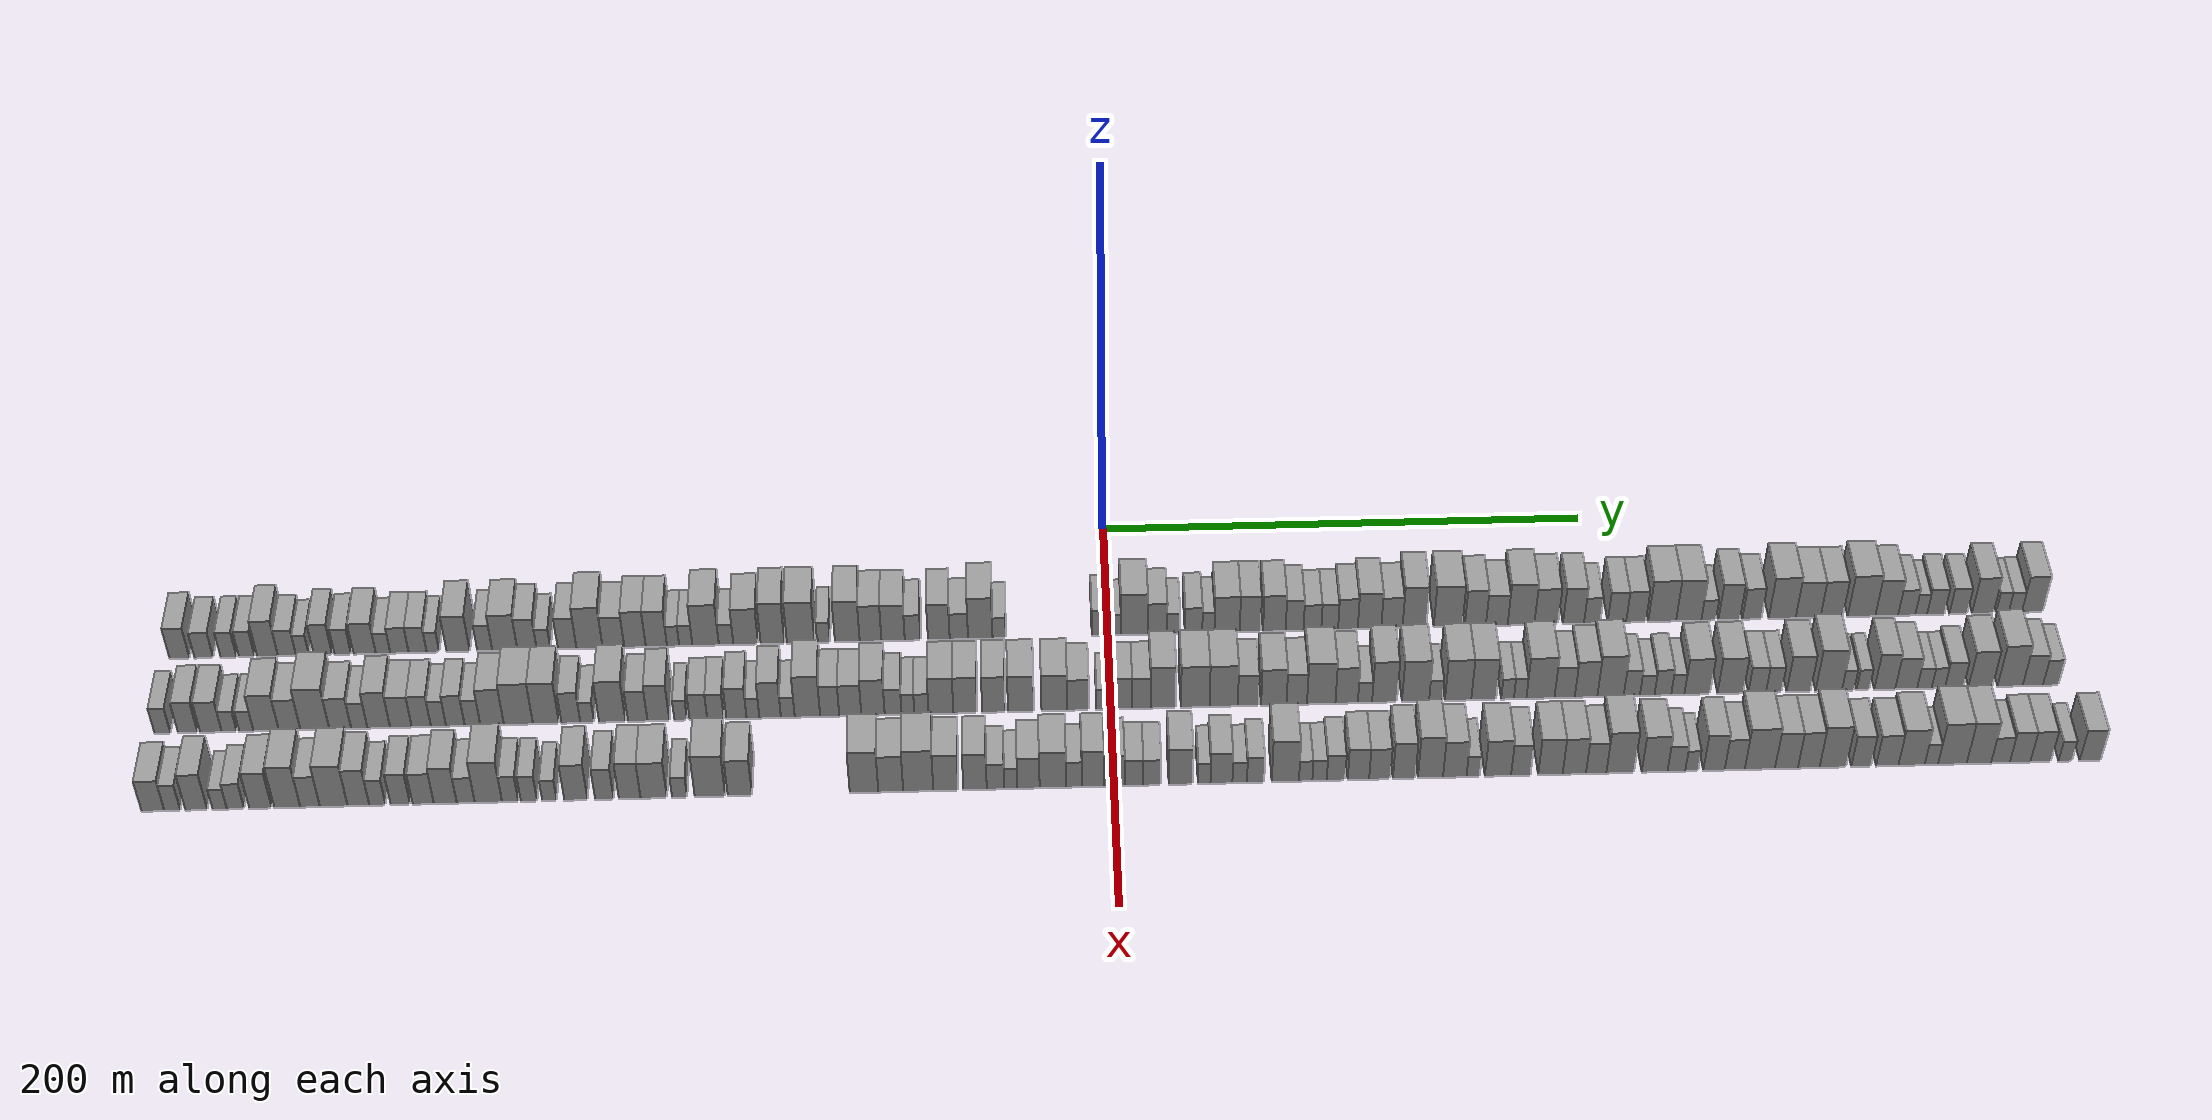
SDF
<sdf version="1.6">
 <world name="default">
  <scene>
   <sky><clouds><speed>12</speed></clouds></sky>
   <ambient>0.4 0.4 0.4 1</ambient>
   <background>0.7 0.7 0.7 1</background>
   <shadows>1</shadows>
  </scene>
  <gravity>0 0 -9.8066</gravity>
  <magnetic_field>6e-06 2.3e-05 -4.2e-05</magnetic_field>
  <physics default="0" name="default_physics" type="ode">
   <ode>
    <solver>
     <type>quick</type>
     <iters>10</iters>
     <sor>1.0</sor>
     <use_dynamic_moi_rescaling>0</use_dynamic_moi_rescaling>
    </solver>
    <constraints>
     <cfm>0</cfm>
     <erp>0.2</erp>
     <contact_max_correcting_vel>100</contact_max_correcting_vel>
     <contact_surface_layer>0.001</contact_surface_layer>
    </constraints>
   </ode>
   <max_step_size>0.004</max_step_size>
   <real_time_factor>1</real_time_factor>
   <real_time_update_rate>250</real_time_update_rate>
  </physics>
  <light name="sun" type="directional">
   <pose>0 0 10 0 0 0</pose>
   <diffuse>0.8 0.8 0.8 1</diffuse>
   <specular>0.2 0.2 0.2 1</specular>
   <attenuation>
    <range>1000</range>
    <constant>0.9</constant>
    <linear>0.01</linear>
    <quadratic>0.001</quadratic>
   </attenuation>
   <direction>-0.5 0.1 -0.9</direction>
  </light>
  <model name="building_1">
   <static>1</static>
   <pose>50.0000 -375.9654 0 0.000000 0.000000 0.000000</pose>
   <link name="link">
    <pose>0 0 9.00 0 0 0</pose>
    <collision name="collision"><geometry><box><size>20.0000 8.0692 18.0000</size></box></geometry></collision>
    <visual name="visual">
     <cast_shadows>0</cast_shadows>
     <geometry><box><size>20.0000 8.0692 18.0000</size></box></geometry>
     <material>
      <script>
       <uri>model://grey_wall/materials/scripts</uri>
       <uri>model://grey_wall/materials/textures</uri>
       <name>vrc/grey_wall</name>
      </script>
     </material>
    </visual>
   </link>
  </model>
  <model name="building_2">
   <static>1</static>
   <pose>50.0000 -366.1815 0 0.000000 0.000000 0.000000</pose>
   <link name="link">
    <pose>0 0 7.50 0 0 0</pose>
    <collision name="collision"><geometry><box><size>20.0000 7.4985 15.0000</size></box></geometry></collision>
    <visual name="visual">
     <cast_shadows>0</cast_shadows>
     <geometry><box><size>20.0000 7.4985 15.0000</size></box></geometry>
     <material>
      <script>
       <uri>model://grey_wall/materials/scripts</uri>
       <uri>model://grey_wall/materials/textures</uri>
       <name>vrc/grey_wall</name>
      </script>
     </material>
    </visual>
   </link>
  </model>
  <model name="building_3">
   <static>1</static>
   <pose>50.0000 -356.2268 0 0.000000 0.000000 0.000000</pose>
   <link name="link">
    <pose>0 0 7.50 0 0 0</pose>
    <collision name="collision"><geometry><box><size>20.0000 6.4109 15.0000</size></box></geometry></collision>
    <visual name="visual">
     <cast_shadows>0</cast_shadows>
     <geometry><box><size>20.0000 6.4109 15.0000</size></box></geometry>
     <material>
      <script>
       <uri>model://grey_wall/materials/scripts</uri>
       <uri>model://grey_wall/materials/textures</uri>
       <name>vrc/grey_wall</name>
      </script>
     </material>
    </visual>
   </link>
  </model>
  <model name="building_4">
   <static>1</static>
   <pose>50.0000 -348.8674 0 0.000000 0.000000 0.000000</pose>
   <link name="link">
    <pose>0 0 7.50 0 0 0</pose>
    <collision name="collision"><geometry><box><size>20.0000 6.3079 15.0000</size></box></geometry></collision>
    <visual name="visual">
     <cast_shadows>0</cast_shadows>
     <geometry><box><size>20.0000 6.3079 15.0000</size></box></geometry>
     <material>
      <script>
       <uri>model://grey_wall/materials/scripts</uri>
       <uri>model://grey_wall/materials/textures</uri>
       <name>vrc/grey_wall</name>
      </script>
     </material>
    </visual>
   </link>
  </model>
  <model name="building_5">
   <static>1</static>
   <pose>50.0000 -340.4998 0 0.000000 0.000000 0.000000</pose>
   <link name="link">
    <pose>0 0 10.50 0 0 0</pose>
    <collision name="collision"><geometry><box><size>20.0000 8.4273 21.0000</size></box></geometry></collision>
    <visual name="visual">
     <cast_shadows>0</cast_shadows>
     <geometry><box><size>20.0000 8.4273 21.0000</size></box></geometry>
     <material>
      <script>
       <uri>model://grey_wall/materials/scripts</uri>
       <uri>model://grey_wall/materials/textures</uri>
       <name>vrc/grey_wall</name>
      </script>
     </material>
    </visual>
   </link>
  </model>
  <model name="building_6">
   <static>1</static>
   <pose>50.0000 -332.6491 0 0.000000 0.000000 0.000000</pose>
   <link name="link">
    <pose>0 0 7.50 0 0 0</pose>
    <collision name="collision"><geometry><box><size>20.0000 7.2742 15.0000</size></box></geometry></collision>
    <visual name="visual">
     <cast_shadows>0</cast_shadows>
     <geometry><box><size>20.0000 7.2742 15.0000</size></box></geometry>
     <material>
      <script>
       <uri>model://grey_wall/materials/scripts</uri>
       <uri>model://grey_wall/materials/textures</uri>
       <name>vrc/grey_wall</name>
      </script>
     </material>
    </visual>
   </link>
  </model>
  <model name="building_7">
   <static>1</static>
   <pose>50.0000 -326.4357 0 0.000000 0.000000 0.000000</pose>
   <link name="link">
    <pose>0 0 6.00 0 0 0</pose>
    <collision name="collision"><geometry><box><size>20.0000 5.1526 12.0000</size></box></geometry></collision>
    <visual name="visual">
     <cast_shadows>0</cast_shadows>
     <geometry><box><size>20.0000 5.1526 12.0000</size></box></geometry>
     <material>
      <script>
       <uri>model://grey_wall/materials/scripts</uri>
       <uri>model://grey_wall/materials/textures</uri>
       <name>vrc/grey_wall</name>
      </script>
     </material>
    </visual>
   </link>
  </model>
  <model name="building_8">
   <static>1</static>
   <pose>50.0000 -318.1620 0 0.000000 0.000000 0.000000</pose>
   <link name="link">
    <pose>0 0 9.00 0 0 0</pose>
    <collision name="collision"><geometry><box><size>20.0000 7.3948 18.0000</size></box></geometry></collision>
    <visual name="visual">
     <cast_shadows>0</cast_shadows>
     <geometry><box><size>20.0000 7.3948 18.0000</size></box></geometry>
     <material>
      <script>
       <uri>model://grey_wall/materials/scripts</uri>
       <uri>model://grey_wall/materials/textures</uri>
       <name>vrc/grey_wall</name>
      </script>
     </material>
    </visual>
   </link>
  </model>
  <model name="building_9">
   <static>1</static>
   <pose>50.0000 -310.1346 0 0.000000 0.000000 0.000000</pose>
   <link name="link">
    <pose>0 0 7.50 0 0 0</pose>
    <collision name="collision"><geometry><box><size>20.0000 6.6600 15.0000</size></box></geometry></collision>
    <visual name="visual">
     <cast_shadows>0</cast_shadows>
     <geometry><box><size>20.0000 6.6600 15.0000</size></box></geometry>
     <material>
      <script>
       <uri>model://grey_wall/materials/scripts</uri>
       <uri>model://grey_wall/materials/textures</uri>
       <name>vrc/grey_wall</name>
      </script>
     </material>
    </visual>
   </link>
  </model>
  <model name="building_10">
   <static>1</static>
   <pose>50.0000 -301.3234 0 0.000000 0.000000 0.000000</pose>
   <link name="link">
    <pose>0 0 9.00 0 0 0</pose>
    <collision name="collision"><geometry><box><size>20.0000 8.9625 18.0000</size></box></geometry></collision>
    <visual name="visual">
     <cast_shadows>0</cast_shadows>
     <geometry><box><size>20.0000 8.9625 18.0000</size></box></geometry>
     <material>
      <script>
       <uri>model://grey_wall/materials/scripts</uri>
       <uri>model://grey_wall/materials/textures</uri>
       <name>vrc/grey_wall</name>
      </script>
     </material>
    </visual>
   </link>
  </model>
  <model name="building_11">
   <static>1</static>
   <pose>50.0000 -293.9074 0 0.000000 0.000000 0.000000</pose>
   <link name="link">
    <pose>0 0 6.00 0 0 0</pose>
    <collision name="collision"><geometry><box><size>20.0000 5.8694 12.0000</size></box></geometry></collision>
    <visual name="visual">
     <cast_shadows>0</cast_shadows>
     <geometry><box><size>20.0000 5.8694 12.0000</size></box></geometry>
     <material>
      <script>
       <uri>model://grey_wall/materials/scripts</uri>
       <uri>model://grey_wall/materials/textures</uri>
       <name>vrc/grey_wall</name>
      </script>
     </material>
    </visual>
   </link>
  </model>
  <model name="building_12">
   <static>1</static>
   <pose>50.0000 -287.2578 0 0.000000 0.000000 0.000000</pose>
   <link name="link">
    <pose>0 0 7.50 0 0 0</pose>
    <collision name="collision"><geometry><box><size>20.0000 7.4297 15.0000</size></box></geometry></collision>
    <visual name="visual">
     <cast_shadows>0</cast_shadows>
     <geometry><box><size>20.0000 7.4297 15.0000</size></box></geometry>
     <material>
      <script>
       <uri>model://grey_wall/materials/scripts</uri>
       <uri>model://grey_wall/materials/textures</uri>
       <name>vrc/grey_wall</name>
      </script>
     </material>
    </visual>
   </link>
  </model>
  <model name="building_13">
   <static>1</static>
   <pose>50.0000 -279.9120 0 0.000000 0.000000 0.000000</pose>
   <link name="link">
    <pose>0 0 7.50 0 0 0</pose>
    <collision name="collision"><geometry><box><size>20.0000 7.2620 15.0000</size></box></geometry></collision>
    <visual name="visual">
     <cast_shadows>0</cast_shadows>
     <geometry><box><size>20.0000 7.2620 15.0000</size></box></geometry>
     <material>
      <script>
       <uri>model://grey_wall/materials/scripts</uri>
       <uri>model://grey_wall/materials/textures</uri>
       <name>vrc/grey_wall</name>
      </script>
     </material>
    </visual>
   </link>
  </model>
  <model name="building_14">
   <static>1</static>
   <pose>50.0000 -273.7572 0 0.000000 0.000000 0.000000</pose>
   <link name="link">
    <pose>0 0 6.00 0 0 0</pose>
    <collision name="collision"><geometry><box><size>20.0000 5.0476 12.0000</size></box></geometry></collision>
    <visual name="visual">
     <cast_shadows>0</cast_shadows>
     <geometry><box><size>20.0000 5.0476 12.0000</size></box></geometry>
     <material>
      <script>
       <uri>model://grey_wall/materials/scripts</uri>
       <uri>model://grey_wall/materials/textures</uri>
       <name>vrc/grey_wall</name>
      </script>
     </material>
    </visual>
   </link>
  </model>
  <model name="building_15">
   <static>1</static>
   <pose>50.0000 -263.5407 0 0.000000 0.000000 0.000000</pose>
   <link name="link">
    <pose>0 0 10.50 0 0 0</pose>
    <collision name="collision"><geometry><box><size>20.0000 9.3854 21.0000</size></box></geometry></collision>
    <visual name="visual">
     <cast_shadows>0</cast_shadows>
     <geometry><box><size>20.0000 9.3854 21.0000</size></box></geometry>
     <material>
      <script>
       <uri>model://grey_wall/materials/scripts</uri>
       <uri>model://grey_wall/materials/textures</uri>
       <name>vrc/grey_wall</name>
      </script>
     </material>
    </visual>
   </link>
  </model>
  <model name="building_16">
   <static>1</static>
   <pose>50.0000 -252.7964 0 0.000000 0.000000 0.000000</pose>
   <link name="link">
    <pose>0 0 7.50 0 0 0</pose>
    <collision name="collision"><geometry><box><size>20.0000 6.1031 15.0000</size></box></geometry></collision>
    <visual name="visual">
     <cast_shadows>0</cast_shadows>
     <geometry><box><size>20.0000 6.1031 15.0000</size></box></geometry>
     <material>
      <script>
       <uri>model://grey_wall/materials/scripts</uri>
       <uri>model://grey_wall/materials/textures</uri>
       <name>vrc/grey_wall</name>
      </script>
     </material>
    </visual>
   </link>
  </model>
  <model name="building_17">
   <static>1</static>
   <pose>50.0000 -244.6731 0 0.000000 0.000000 0.000000</pose>
   <link name="link">
    <pose>0 0 10.50 0 0 0</pose>
    <collision name="collision"><geometry><box><size>20.0000 10.1435 21.0000</size></box></geometry></collision>
    <visual name="visual">
     <cast_shadows>0</cast_shadows>
     <geometry><box><size>20.0000 10.1435 21.0000</size></box></geometry>
     <material>
      <script>
       <uri>model://grey_wall/materials/scripts</uri>
       <uri>model://grey_wall/materials/textures</uri>
       <name>vrc/grey_wall</name>
      </script>
     </material>
    </visual>
   </link>
  </model>
  <model name="building_18">
   <static>1</static>
   <pose>50.0000 -235.7101 0 0.000000 0.000000 0.000000</pose>
   <link name="link">
    <pose>0 0 9.00 0 0 0</pose>
    <collision name="collision"><geometry><box><size>20.0000 7.7825 18.0000</size></box></geometry></collision>
    <visual name="visual">
     <cast_shadows>0</cast_shadows>
     <geometry><box><size>20.0000 7.7825 18.0000</size></box></geometry>
     <material>
      <script>
       <uri>model://grey_wall/materials/scripts</uri>
       <uri>model://grey_wall/materials/textures</uri>
       <name>vrc/grey_wall</name>
      </script>
     </material>
    </visual>
   </link>
  </model>
  <model name="building_19">
   <static>1</static>
   <pose>50.0000 -229.0396 0 0.000000 0.000000 0.000000</pose>
   <link name="link">
    <pose>0 0 6.00 0 0 0</pose>
    <collision name="collision"><geometry><box><size>20.0000 5.5586 12.0000</size></box></geometry></collision>
    <visual name="visual">
     <cast_shadows>0</cast_shadows>
     <geometry><box><size>20.0000 5.5586 12.0000</size></box></geometry>
     <material>
      <script>
       <uri>model://grey_wall/materials/scripts</uri>
       <uri>model://grey_wall/materials/textures</uri>
       <name>vrc/grey_wall</name>
      </script>
     </material>
    </visual>
   </link>
  </model>
  <model name="building_20">
   <static>1</static>
   <pose>50.0000 -219.4842 0 0.000000 0.000000 0.000000</pose>
   <link name="link">
    <pose>0 0 9.00 0 0 0</pose>
    <collision name="collision"><geometry><box><size>20.0000 7.5521 18.0000</size></box></geometry></collision>
    <visual name="visual">
     <cast_shadows>0</cast_shadows>
     <geometry><box><size>20.0000 7.5521 18.0000</size></box></geometry>
     <material>
      <script>
       <uri>model://grey_wall/materials/scripts</uri>
       <uri>model://grey_wall/materials/textures</uri>
       <name>vrc/grey_wall</name>
      </script>
     </material>
    </visual>
   </link>
  </model>
  <model name="building_21">
   <static>1</static>
   <pose>50.0000 -210.4053 0 0.000000 0.000000 0.000000</pose>
   <link name="link">
    <pose>0 0 12.00 0 0 0</pose>
    <collision name="collision"><geometry><box><size>20.0000 10.6058 24.0000</size></box></geometry></collision>
    <visual name="visual">
     <cast_shadows>0</cast_shadows>
     <geometry><box><size>20.0000 10.6058 24.0000</size></box></geometry>
     <material>
      <script>
       <uri>model://grey_wall/materials/scripts</uri>
       <uri>model://grey_wall/materials/textures</uri>
       <name>vrc/grey_wall</name>
      </script>
     </material>
    </visual>
   </link>
  </model>
  <model name="building_22">
   <static>1</static>
   <pose>50.0000 -200.7312 0 0.000000 0.000000 0.000000</pose>
   <link name="link">
    <pose>0 0 9.00 0 0 0</pose>
    <collision name="collision"><geometry><box><size>20.0000 8.7424 18.0000</size></box></geometry></collision>
    <visual name="visual">
     <cast_shadows>0</cast_shadows>
     <geometry><box><size>20.0000 8.7424 18.0000</size></box></geometry>
     <material>
      <script>
       <uri>model://grey_wall/materials/scripts</uri>
       <uri>model://grey_wall/materials/textures</uri>
       <name>vrc/grey_wall</name>
      </script>
     </material>
    </visual>
   </link>
  </model>
  <model name="building_23">
   <static>1</static>
   <pose>50.0000 -192.0016 0 0.000000 0.000000 0.000000</pose>
   <link name="link">
    <pose>0 0 10.50 0 0 0</pose>
    <collision name="collision"><geometry><box><size>20.0000 8.7167 21.0000</size></box></geometry></collision>
    <visual name="visual">
     <cast_shadows>0</cast_shadows>
     <geometry><box><size>20.0000 8.7167 21.0000</size></box></geometry>
     <material>
      <script>
       <uri>model://grey_wall/materials/scripts</uri>
       <uri>model://grey_wall/materials/textures</uri>
       <name>vrc/grey_wall</name>
      </script>
     </material>
    </visual>
   </link>
  </model>
  <model name="building_24">
   <static>1</static>
   <pose>50.0000 -183.3436 0 0.000000 0.000000 0.000000</pose>
   <link name="link">
    <pose>0 0 10.50 0 0 0</pose>
    <collision name="collision"><geometry><box><size>20.0000 8.5995 21.0000</size></box></geometry></collision>
    <visual name="visual">
     <cast_shadows>0</cast_shadows>
     <geometry><box><size>20.0000 8.5995 21.0000</size></box></geometry>
     <material>
      <script>
       <uri>model://grey_wall/materials/scripts</uri>
       <uri>model://grey_wall/materials/textures</uri>
       <name>vrc/grey_wall</name>
      </script>
     </material>
    </visual>
   </link>
  </model>
  <model name="building_25">
   <static>1</static>
   <pose>50.0000 -176.5685 0 0.000000 0.000000 0.000000</pose>
   <link name="link">
    <pose>0 0 6.00 0 0 0</pose>
    <collision name="collision"><geometry><box><size>20.0000 4.9507 12.0000</size></box></geometry></collision>
    <visual name="visual">
     <cast_shadows>0</cast_shadows>
     <geometry><box><size>20.0000 4.9507 12.0000</size></box></geometry>
     <material>
      <script>
       <uri>model://grey_wall/materials/scripts</uri>
       <uri>model://grey_wall/materials/textures</uri>
       <name>vrc/grey_wall</name>
      </script>
     </material>
    </visual>
   </link>
  </model>
  <model name="building_26">
   <static>1</static>
   <pose>50.0000 -171.4349 0 0.000000 0.000000 0.000000</pose>
   <link name="link">
    <pose>0 0 6.00 0 0 0</pose>
    <collision name="collision"><geometry><box><size>20.0000 5.3165 12.0000</size></box></geometry></collision>
    <visual name="visual">
     <cast_shadows>0</cast_shadows>
     <geometry><box><size>20.0000 5.3165 12.0000</size></box></geometry>
     <material>
      <script>
       <uri>model://grey_wall/materials/scripts</uri>
       <uri>model://grey_wall/materials/textures</uri>
       <name>vrc/grey_wall</name>
      </script>
     </material>
    </visual>
   </link>
  </model>
  <model name="building_27">
   <static>1</static>
   <pose>50.0000 -163.4091 0 0.000000 0.000000 0.000000</pose>
   <link name="link">
    <pose>0 0 12.00 0 0 0</pose>
    <collision name="collision"><geometry><box><size>20.0000 10.7351 24.0000</size></box></geometry></collision>
    <visual name="visual">
     <cast_shadows>0</cast_shadows>
     <geometry><box><size>20.0000 10.7351 24.0000</size></box></geometry>
     <material>
      <script>
       <uri>model://grey_wall/materials/scripts</uri>
       <uri>model://grey_wall/materials/textures</uri>
       <name>vrc/grey_wall</name>
      </script>
     </material>
    </visual>
   </link>
  </model>
  <model name="building_28">
   <static>1</static>
   <pose>50.0000 -155.1005 0 0.000000 0.000000 0.000000</pose>
   <link name="link">
    <pose>0 0 6.00 0 0 0</pose>
    <collision name="collision"><geometry><box><size>20.0000 5.8822 12.0000</size></box></geometry></collision>
    <visual name="visual">
     <cast_shadows>0</cast_shadows>
     <geometry><box><size>20.0000 5.8822 12.0000</size></box></geometry>
     <material>
      <script>
       <uri>model://grey_wall/materials/scripts</uri>
       <uri>model://grey_wall/materials/textures</uri>
       <name>vrc/grey_wall</name>
      </script>
     </material>
    </visual>
   </link>
  </model>
  <model name="building_29">
   <static>1</static>
   <pose>50.0000 -147.1350 0 0.000000 0.000000 0.000000</pose>
   <link name="link">
    <pose>0 0 10.50 0 0 0</pose>
    <collision name="collision"><geometry><box><size>20.0000 10.0487 21.0000</size></box></geometry></collision>
    <visual name="visual">
     <cast_shadows>0</cast_shadows>
     <geometry><box><size>20.0000 10.0487 21.0000</size></box></geometry>
     <material>
      <script>
       <uri>model://grey_wall/materials/scripts</uri>
       <uri>model://grey_wall/materials/textures</uri>
       <name>vrc/grey_wall</name>
      </script>
     </material>
    </visual>
   </link>
  </model>
  <model name="building_30">
   <static>1</static>
   <pose>50.0000 -136.2777 0 0.000000 0.000000 0.000000</pose>
   <link name="link">
    <pose>0 0 12.00 0 0 0</pose>
    <collision name="collision"><geometry><box><size>20.0000 9.6658 24.0000</size></box></geometry></collision>
    <visual name="visual">
     <cast_shadows>0</cast_shadows>
     <geometry><box><size>20.0000 9.6658 24.0000</size></box></geometry>
     <material>
      <script>
       <uri>model://grey_wall/materials/scripts</uri>
       <uri>model://grey_wall/materials/textures</uri>
       <name>vrc/grey_wall</name>
      </script>
     </material>
    </visual>
   </link>
  </model>
  <model name="building_31">
   <static>1</static>
   <pose>50.0000 -124.8210 0 0.000000 0.000000 0.000000</pose>
   <link name="link">
    <pose>0 0 12.00 0 0 0</pose>
    <collision name="collision"><geometry><box><size>20.0000 11.2476 24.0000</size></box></geometry></collision>
    <visual name="visual">
     <cast_shadows>0</cast_shadows>
     <geometry><box><size>20.0000 11.2476 24.0000</size></box></geometry>
     <material>
      <script>
       <uri>model://grey_wall/materials/scripts</uri>
       <uri>model://grey_wall/materials/textures</uri>
       <name>vrc/grey_wall</name>
      </script>
     </material>
    </visual>
   </link>
  </model>
  <model name="building_32">
   <static>1</static>
   <pose>50.0000 -115.5725 0 0.000000 0.000000 0.000000</pose>
   <link name="link">
    <pose>0 0 6.00 0 0 0</pose>
    <collision name="collision"><geometry><box><size>20.0000 5.2493 12.0000</size></box></geometry></collision>
    <visual name="visual">
     <cast_shadows>0</cast_shadows>
     <geometry><box><size>20.0000 5.2493 12.0000</size></box></geometry>
     <material>
      <script>
       <uri>model://grey_wall/materials/scripts</uri>
       <uri>model://grey_wall/materials/textures</uri>
       <name>vrc/grey_wall</name>
      </script>
     </material>
    </visual>
   </link>
  </model>
  <model name="building_33">
   <static>1</static>
   <pose>50.0000 -105.9204 0 0.000000 0.000000 0.000000</pose>
   <link name="link">
    <pose>0 0 12.00 0 0 0</pose>
    <collision name="collision"><geometry><box><size>20.0000 10.0549 24.0000</size></box></geometry></collision>
    <visual name="visual">
     <cast_shadows>0</cast_shadows>
     <geometry><box><size>20.0000 10.0549 24.0000</size></box></geometry>
     <material>
      <script>
       <uri>model://grey_wall/materials/scripts</uri>
       <uri>model://grey_wall/materials/textures</uri>
       <name>vrc/grey_wall</name>
      </script>
     </material>
    </visual>
   </link>
  </model>
  <model name="building_34">
   <static>1</static>
   <pose>50.0000 -96.4681 0 0.000000 0.000000 0.000000</pose>
   <link name="link">
    <pose>0 0 10.50 0 0 0</pose>
    <collision name="collision"><geometry><box><size>20.0000 8.8497 21.0000</size></box></geometry></collision>
    <visual name="visual">
     <cast_shadows>0</cast_shadows>
     <geometry><box><size>20.0000 8.8497 21.0000</size></box></geometry>
     <material>
      <script>
       <uri>model://grey_wall/materials/scripts</uri>
       <uri>model://grey_wall/materials/textures</uri>
       <name>vrc/grey_wall</name>
      </script>
     </material>
    </visual>
   </link>
  </model>
  <model name="building_35">
   <static>1</static>
   <pose>50.0000 -87.3076 0 0.000000 0.000000 0.000000</pose>
   <link name="link">
    <pose>0 0 10.50 0 0 0</pose>
    <collision name="collision"><geometry><box><size>20.0000 9.4713 21.0000</size></box></geometry></collision>
    <visual name="visual">
     <cast_shadows>0</cast_shadows>
     <geometry><box><size>20.0000 9.4713 21.0000</size></box></geometry>
     <material>
      <script>
       <uri>model://grey_wall/materials/scripts</uri>
       <uri>model://grey_wall/materials/textures</uri>
       <name>vrc/grey_wall</name>
      </script>
     </material>
    </visual>
   </link>
  </model>
  <model name="building_36">
   <static>1</static>
   <pose>50.0000 -79.3680 0 0.000000 0.000000 0.000000</pose>
   <link name="link">
    <pose>0 0 7.50 0 0 0</pose>
    <collision name="collision"><geometry><box><size>20.0000 6.4079 15.0000</size></box></geometry></collision>
    <visual name="visual">
     <cast_shadows>0</cast_shadows>
     <geometry><box><size>20.0000 6.4079 15.0000</size></box></geometry>
     <material>
      <script>
       <uri>model://grey_wall/materials/scripts</uri>
       <uri>model://grey_wall/materials/textures</uri>
       <name>vrc/grey_wall</name>
      </script>
     </material>
    </visual>
   </link>
  </model>
  <model name="building_37">
   <static>1</static>
   <pose>50.0000 -68.7371 0 0.000000 0.000000 0.000000</pose>
   <link name="link">
    <pose>0 0 10.50 0 0 0</pose>
    <collision name="collision"><geometry><box><size>20.0000 8.8539 21.0000</size></box></geometry></collision>
    <visual name="visual">
     <cast_shadows>0</cast_shadows>
     <geometry><box><size>20.0000 8.8539 21.0000</size></box></geometry>
     <material>
      <script>
       <uri>model://grey_wall/materials/scripts</uri>
       <uri>model://grey_wall/materials/textures</uri>
       <name>vrc/grey_wall</name>
      </script>
     </material>
    </visual>
   </link>
  </model>
  <model name="building_38">
   <static>1</static>
   <pose>50.0000 -60.5868 0 0.000000 0.000000 0.000000</pose>
   <link name="link">
    <pose>0 0 7.50 0 0 0</pose>
    <collision name="collision"><geometry><box><size>20.0000 7.4467 15.0000</size></box></geometry></collision>
    <visual name="visual">
     <cast_shadows>0</cast_shadows>
     <geometry><box><size>20.0000 7.4467 15.0000</size></box></geometry>
     <material>
      <script>
       <uri>model://grey_wall/materials/scripts</uri>
       <uri>model://grey_wall/materials/textures</uri>
       <name>vrc/grey_wall</name>
      </script>
     </material>
    </visual>
   </link>
  </model>
  <model name="building_39">
   <static>1</static>
   <pose>50.0000 -51.8741 0 0.000000 0.000000 0.000000</pose>
   <link name="link">
    <pose>0 0 12.00 0 0 0</pose>
    <collision name="collision"><geometry><box><size>20.0000 9.9787 24.0000</size></box></geometry></collision>
    <visual name="visual">
     <cast_shadows>0</cast_shadows>
     <geometry><box><size>20.0000 9.9787 24.0000</size></box></geometry>
     <material>
      <script>
       <uri>model://grey_wall/materials/scripts</uri>
       <uri>model://grey_wall/materials/textures</uri>
       <name>vrc/grey_wall</name>
      </script>
     </material>
    </visual>
   </link>
  </model>
  <model name="building_40">
   <static>1</static>
   <pose>50.0000 -44.1848 0 0.000000 0.000000 0.000000</pose>
   <link name="link">
    <pose>0 0 6.00 0 0 0</pose>
    <collision name="collision"><geometry><box><size>20.0000 5.3999 12.0000</size></box></geometry></collision>
    <visual name="visual">
     <cast_shadows>0</cast_shadows>
     <geometry><box><size>20.0000 5.3999 12.0000</size></box></geometry>
     <material>
      <script>
       <uri>model://grey_wall/materials/scripts</uri>
       <uri>model://grey_wall/materials/textures</uri>
       <name>vrc/grey_wall</name>
      </script>
     </material>
    </visual>
   </link>
  </model>
  <model name="building_41">
   <static>1</static>
   <pose>50.0000 -2.9925 0 0.000000 0.000000 0.000000</pose>
   <link name="link">
    <pose>0 0 7.50 0 0 0</pose>
    <collision name="collision"><geometry><box><size>20.0000 6.9949 15.0000</size></box></geometry></collision>
    <visual name="visual">
     <cast_shadows>0</cast_shadows>
     <geometry><box><size>20.0000 6.9949 15.0000</size></box></geometry>
     <material>
      <script>
       <uri>model://grey_wall/materials/scripts</uri>
       <uri>model://grey_wall/materials/textures</uri>
       <name>vrc/grey_wall</name>
      </script>
     </material>
    </visual>
   </link>
  </model>
  <model name="building_42">
   <static>1</static>
   <pose>50.0000 2.9377 0 0.000000 0.000000 0.000000</pose>
   <link name="link">
    <pose>0 0 6.00 0 0 0</pose>
    <collision name="collision"><geometry><box><size>20.0000 4.8656 12.0000</size></box></geometry></collision>
    <visual name="visual">
     <cast_shadows>0</cast_shadows>
     <geometry><box><size>20.0000 4.8656 12.0000</size></box></geometry>
     <material>
      <script>
       <uri>model://grey_wall/materials/scripts</uri>
       <uri>model://grey_wall/materials/textures</uri>
       <name>vrc/grey_wall</name>
      </script>
     </material>
    </visual>
   </link>
  </model>
  <model name="building_43">
   <static>1</static>
   <pose>50.0000 10.8347 0 0.000000 0.000000 0.000000</pose>
   <link name="link">
    <pose>0 0 12.00 0 0 0</pose>
    <collision name="collision"><geometry><box><size>20.0000 10.9284 24.0000</size></box></geometry></collision>
    <visual name="visual">
     <cast_shadows>0</cast_shadows>
     <geometry><box><size>20.0000 10.9284 24.0000</size></box></geometry>
     <material>
      <script>
       <uri>model://grey_wall/materials/scripts</uri>
       <uri>model://grey_wall/materials/textures</uri>
       <name>vrc/grey_wall</name>
      </script>
     </material>
    </visual>
   </link>
  </model>
  <model name="building_44">
   <static>1</static>
   <pose>50.0000 20.2627 0 0.000000 0.000000 0.000000</pose>
   <link name="link">
    <pose>0 0 9.00 0 0 0</pose>
    <collision name="collision"><geometry><box><size>20.0000 7.9275 18.0000</size></box></geometry></collision>
    <visual name="visual">
     <cast_shadows>0</cast_shadows>
     <geometry><box><size>20.0000 7.9275 18.0000</size></box></geometry>
     <material>
      <script>
       <uri>model://grey_wall/materials/scripts</uri>
       <uri>model://grey_wall/materials/textures</uri>
       <name>vrc/grey_wall</name>
      </script>
     </material>
    </visual>
   </link>
  </model>
  <model name="building_45">
   <static>1</static>
   <pose>50.0000 26.8715 0 0.000000 0.000000 0.000000</pose>
   <link name="link">
    <pose>0 0 6.00 0 0 0</pose>
    <collision name="collision"><geometry><box><size>20.0000 5.2903 12.0000</size></box></geometry></collision>
    <visual name="visual">
     <cast_shadows>0</cast_shadows>
     <geometry><box><size>20.0000 5.2903 12.0000</size></box></geometry>
     <material>
      <script>
       <uri>model://grey_wall/materials/scripts</uri>
       <uri>model://grey_wall/materials/textures</uri>
       <name>vrc/grey_wall</name>
      </script>
     </material>
    </visual>
   </link>
  </model>
  <model name="building_46">
   <static>1</static>
   <pose>50.0000 35.0334 0 0.000000 0.000000 0.000000</pose>
   <link name="link">
    <pose>0 0 7.50 0 0 0</pose>
    <collision name="collision"><geometry><box><size>20.0000 7.0335 15.0000</size></box></geometry></collision>
    <visual name="visual">
     <cast_shadows>0</cast_shadows>
     <geometry><box><size>20.0000 7.0335 15.0000</size></box></geometry>
     <material>
      <script>
       <uri>model://grey_wall/materials/scripts</uri>
       <uri>model://grey_wall/materials/textures</uri>
       <name>vrc/grey_wall</name>
      </script>
     </material>
    </visual>
   </link>
  </model>
  <model name="building_47">
   <static>1</static>
   <pose>50.0000 41.0266 0 0.000000 0.000000 0.000000</pose>
   <link name="link">
    <pose>0 0 6.00 0 0 0</pose>
    <collision name="collision"><geometry><box><size>20.0000 4.9528 12.0000</size></box></geometry></collision>
    <visual name="visual">
     <cast_shadows>0</cast_shadows>
     <geometry><box><size>20.0000 4.9528 12.0000</size></box></geometry>
     <material>
      <script>
       <uri>model://grey_wall/materials/scripts</uri>
       <uri>model://grey_wall/materials/textures</uri>
       <name>vrc/grey_wall</name>
      </script>
     </material>
    </visual>
   </link>
  </model>
  <model name="building_48">
   <static>1</static>
   <pose>50.0000 48.6818 0 0.000000 0.000000 0.000000</pose>
   <link name="link">
    <pose>0 0 10.50 0 0 0</pose>
    <collision name="collision"><geometry><box><size>20.0000 10.3576 21.0000</size></box></geometry></collision>
    <visual name="visual">
     <cast_shadows>0</cast_shadows>
     <geometry><box><size>20.0000 10.3576 21.0000</size></box></geometry>
     <material>
      <script>
       <uri>model://grey_wall/materials/scripts</uri>
       <uri>model://grey_wall/materials/textures</uri>
       <name>vrc/grey_wall</name>
      </script>
     </material>
    </visual>
   </link>
  </model>
  <model name="building_49">
   <static>1</static>
   <pose>50.0000 58.1059 0 0.000000 0.000000 0.000000</pose>
   <link name="link">
    <pose>0 0 10.50 0 0 0</pose>
    <collision name="collision"><geometry><box><size>20.0000 8.4907 21.0000</size></box></geometry></collision>
    <visual name="visual">
     <cast_shadows>0</cast_shadows>
     <geometry><box><size>20.0000 8.4907 21.0000</size></box></geometry>
     <material>
      <script>
       <uri>model://grey_wall/materials/scripts</uri>
       <uri>model://grey_wall/materials/textures</uri>
       <name>vrc/grey_wall</name>
      </script>
     </material>
    </visual>
   </link>
  </model>
  <model name="building_50">
   <static>1</static>
   <pose>50.0000 67.9712 0 0.000000 0.000000 0.000000</pose>
   <link name="link">
    <pose>0 0 10.50 0 0 0</pose>
    <collision name="collision"><geometry><box><size>20.0000 9.2398 21.0000</size></box></geometry></collision>
    <visual name="visual">
     <cast_shadows>0</cast_shadows>
     <geometry><box><size>20.0000 9.2398 21.0000</size></box></geometry>
     <material>
      <script>
       <uri>model://grey_wall/materials/scripts</uri>
       <uri>model://grey_wall/materials/textures</uri>
       <name>vrc/grey_wall</name>
      </script>
     </material>
    </visual>
   </link>
  </model>
  <model name="building_51">
   <static>1</static>
   <pose>50.0000 76.2383 0 0.000000 0.000000 0.000000</pose>
   <link name="link">
    <pose>0 0 9.00 0 0 0</pose>
    <collision name="collision"><geometry><box><size>20.0000 7.2944 18.0000</size></box></geometry></collision>
    <visual name="visual">
     <cast_shadows>0</cast_shadows>
     <geometry><box><size>20.0000 7.2944 18.0000</size></box></geometry>
     <material>
      <script>
       <uri>model://grey_wall/materials/scripts</uri>
       <uri>model://grey_wall/materials/textures</uri>
       <name>vrc/grey_wall</name>
      </script>
     </material>
    </visual>
   </link>
  </model>
  <model name="building_52">
   <static>1</static>
   <pose>50.0000 83.5238 0 0.000000 0.000000 0.000000</pose>
   <link name="link">
    <pose>0 0 7.50 0 0 0</pose>
    <collision name="collision"><geometry><box><size>20.0000 7.2766 15.0000</size></box></geometry></collision>
    <visual name="visual">
     <cast_shadows>0</cast_shadows>
     <geometry><box><size>20.0000 7.2766 15.0000</size></box></geometry>
     <material>
      <script>
       <uri>model://grey_wall/materials/scripts</uri>
       <uri>model://grey_wall/materials/textures</uri>
       <name>vrc/grey_wall</name>
      </script>
     </material>
    </visual>
   </link>
  </model>
  <model name="building_53">
   <static>1</static>
   <pose>50.0000 90.5950 0 0.000000 0.000000 0.000000</pose>
   <link name="link">
    <pose>0 0 7.50 0 0 0</pose>
    <collision name="collision"><geometry><box><size>20.0000 6.8658 15.0000</size></box></geometry></collision>
    <visual name="visual">
     <cast_shadows>0</cast_shadows>
     <geometry><box><size>20.0000 6.8658 15.0000</size></box></geometry>
     <material>
      <script>
       <uri>model://grey_wall/materials/scripts</uri>
       <uri>model://grey_wall/materials/textures</uri>
       <name>vrc/grey_wall</name>
      </script>
     </material>
    </visual>
   </link>
  </model>
  <model name="building_54">
   <static>1</static>
   <pose>50.0000 98.0356 0 0.000000 0.000000 0.000000</pose>
   <link name="link">
    <pose>0 0 9.00 0 0 0</pose>
    <collision name="collision"><geometry><box><size>20.0000 8.0153 18.0000</size></box></geometry></collision>
    <visual name="visual">
     <cast_shadows>0</cast_shadows>
     <geometry><box><size>20.0000 8.0153 18.0000</size></box></geometry>
     <material>
      <script>
       <uri>model://grey_wall/materials/scripts</uri>
       <uri>model://grey_wall/materials/textures</uri>
       <name>vrc/grey_wall</name>
      </script>
     </material>
    </visual>
   </link>
  </model>
  <model name="building_55">
   <static>1</static>
   <pose>50.0000 106.8641 0 0.000000 0.000000 0.000000</pose>
   <link name="link">
    <pose>0 0 10.50 0 0 0</pose>
    <collision name="collision"><geometry><box><size>20.0000 9.6418 21.0000</size></box></geometry></collision>
    <visual name="visual">
     <cast_shadows>0</cast_shadows>
     <geometry><box><size>20.0000 9.6418 21.0000</size></box></geometry>
     <material>
      <script>
       <uri>model://grey_wall/materials/scripts</uri>
       <uri>model://grey_wall/materials/textures</uri>
       <name>vrc/grey_wall</name>
      </script>
     </material>
    </visual>
   </link>
  </model>
  <model name="building_56">
   <static>1</static>
   <pose>50.0000 116.0233 0 0.000000 0.000000 0.000000</pose>
   <link name="link">
    <pose>0 0 9.00 0 0 0</pose>
    <collision name="collision"><geometry><box><size>20.0000 8.6765 18.0000</size></box></geometry></collision>
    <visual name="visual">
     <cast_shadows>0</cast_shadows>
     <geometry><box><size>20.0000 8.6765 18.0000</size></box></geometry>
     <material>
      <script>
       <uri>model://grey_wall/materials/scripts</uri>
       <uri>model://grey_wall/materials/textures</uri>
       <name>vrc/grey_wall</name>
      </script>
     </material>
    </visual>
   </link>
  </model>
  <model name="building_57">
   <static>1</static>
   <pose>50.0000 125.2580 0 0.000000 0.000000 0.000000</pose>
   <link name="link">
    <pose>0 0 12.00 0 0 0</pose>
    <collision name="collision"><geometry><box><size>20.0000 9.7930 24.0000</size></box></geometry></collision>
    <visual name="visual">
     <cast_shadows>0</cast_shadows>
     <geometry><box><size>20.0000 9.7930 24.0000</size></box></geometry>
     <material>
      <script>
       <uri>model://grey_wall/materials/scripts</uri>
       <uri>model://grey_wall/materials/textures</uri>
       <name>vrc/grey_wall</name>
      </script>
     </material>
    </visual>
   </link>
  </model>
  <model name="building_58">
   <static>1</static>
   <pose>50.0000 139.0167 0 0.000000 0.000000 0.000000</pose>
   <link name="link">
    <pose>0 0 12.00 0 0 0</pose>
    <collision name="collision"><geometry><box><size>20.0000 11.7243 24.0000</size></box></geometry></collision>
    <visual name="visual">
     <cast_shadows>0</cast_shadows>
     <geometry><box><size>20.0000 11.7243 24.0000</size></box></geometry>
     <material>
      <script>
       <uri>model://grey_wall/materials/scripts</uri>
       <uri>model://grey_wall/materials/textures</uri>
       <name>vrc/grey_wall</name>
      </script>
     </material>
    </visual>
   </link>
  </model>
  <model name="building_59">
   <static>1</static>
   <pose>50.0000 150.1968 0 0.000000 0.000000 0.000000</pose>
   <link name="link">
    <pose>0 0 10.50 0 0 0</pose>
    <collision name="collision"><geometry><box><size>20.0000 8.6360 21.0000</size></box></geometry></collision>
    <visual name="visual">
     <cast_shadows>0</cast_shadows>
     <geometry><box><size>20.0000 8.6360 21.0000</size></box></geometry>
     <material>
      <script>
       <uri>model://grey_wall/materials/scripts</uri>
       <uri>model://grey_wall/materials/textures</uri>
       <name>vrc/grey_wall</name>
      </script>
     </material>
    </visual>
   </link>
  </model>
  <model name="building_60">
   <static>1</static>
   <pose>50.0000 158.9674 0 0.000000 0.000000 0.000000</pose>
   <link name="link">
    <pose>0 0 9.00 0 0 0</pose>
    <collision name="collision"><geometry><box><size>20.0000 8.9051 18.0000</size></box></geometry></collision>
    <visual name="visual">
     <cast_shadows>0</cast_shadows>
     <geometry><box><size>20.0000 8.9051 18.0000</size></box></geometry>
     <material>
      <script>
       <uri>model://grey_wall/materials/scripts</uri>
       <uri>model://grey_wall/materials/textures</uri>
       <name>vrc/grey_wall</name>
      </script>
     </material>
    </visual>
   </link>
  </model>
  <model name="building_61">
   <static>1</static>
   <pose>50.0000 168.8890 0 0.000000 0.000000 0.000000</pose>
   <link name="link">
    <pose>0 0 12.00 0 0 0</pose>
    <collision name="collision"><geometry><box><size>20.0000 10.9381 24.0000</size></box></geometry></collision>
    <visual name="visual">
     <cast_shadows>0</cast_shadows>
     <geometry><box><size>20.0000 10.9381 24.0000</size></box></geometry>
     <material>
      <script>
       <uri>model://grey_wall/materials/scripts</uri>
       <uri>model://grey_wall/materials/textures</uri>
       <name>vrc/grey_wall</name>
      </script>
     </material>
    </visual>
   </link>
  </model>
  <model name="building_62">
   <static>1</static>
   <pose>50.0000 179.2238 0 0.000000 0.000000 0.000000</pose>
   <link name="link">
    <pose>0 0 10.50 0 0 0</pose>
    <collision name="collision"><geometry><box><size>20.0000 9.7315 21.0000</size></box></geometry></collision>
    <visual name="visual">
     <cast_shadows>0</cast_shadows>
     <geometry><box><size>20.0000 9.7315 21.0000</size></box></geometry>
     <material>
      <script>
       <uri>model://grey_wall/materials/scripts</uri>
       <uri>model://grey_wall/materials/textures</uri>
       <name>vrc/grey_wall</name>
      </script>
     </material>
    </visual>
   </link>
  </model>
  <model name="building_63">
   <static>1</static>
   <pose>50.0000 190.4064 0 0.000000 0.000000 0.000000</pose>
   <link name="link">
    <pose>0 0 10.50 0 0 0</pose>
    <collision name="collision"><geometry><box><size>20.0000 8.6338 21.0000</size></box></geometry></collision>
    <visual name="visual">
     <cast_shadows>0</cast_shadows>
     <geometry><box><size>20.0000 8.6338 21.0000</size></box></geometry>
     <material>
      <script>
       <uri>model://grey_wall/materials/scripts</uri>
       <uri>model://grey_wall/materials/textures</uri>
       <name>vrc/grey_wall</name>
      </script>
     </material>
    </visual>
   </link>
  </model>
  <model name="building_64">
   <static>1</static>
   <pose>50.0000 198.0834 0 0.000000 0.000000 0.000000</pose>
   <link name="link">
    <pose>0 0 7.50 0 0 0</pose>
    <collision name="collision"><geometry><box><size>20.0000 6.7202 15.0000</size></box></geometry></collision>
    <visual name="visual">
     <cast_shadows>0</cast_shadows>
     <geometry><box><size>20.0000 6.7202 15.0000</size></box></geometry>
     <material>
      <script>
       <uri>model://grey_wall/materials/scripts</uri>
       <uri>model://grey_wall/materials/textures</uri>
       <name>vrc/grey_wall</name>
      </script>
     </material>
    </visual>
   </link>
  </model>
  <model name="building_65">
   <static>1</static>
   <pose>50.0000 208.2382 0 0.000000 0.000000 0.000000</pose>
   <link name="link">
    <pose>0 0 9.00 0 0 0</pose>
    <collision name="collision"><geometry><box><size>20.0000 7.5893 18.0000</size></box></geometry></collision>
    <visual name="visual">
     <cast_shadows>0</cast_shadows>
     <geometry><box><size>20.0000 7.5893 18.0000</size></box></geometry>
     <material>
      <script>
       <uri>model://grey_wall/materials/scripts</uri>
       <uri>model://grey_wall/materials/textures</uri>
       <name>vrc/grey_wall</name>
      </script>
     </material>
    </visual>
   </link>
  </model>
  <model name="building_66">
   <static>1</static>
   <pose>50.0000 216.0574 0 0.000000 0.000000 0.000000</pose>
   <link name="link">
    <pose>0 0 9.00 0 0 0</pose>
    <collision name="collision"><geometry><box><size>20.0000 8.0491 18.0000</size></box></geometry></collision>
    <visual name="visual">
     <cast_shadows>0</cast_shadows>
     <geometry><box><size>20.0000 8.0491 18.0000</size></box></geometry>
     <material>
      <script>
       <uri>model://grey_wall/materials/scripts</uri>
       <uri>model://grey_wall/materials/textures</uri>
       <name>vrc/grey_wall</name>
      </script>
     </material>
    </visual>
   </link>
  </model>
  <model name="building_67">
   <static>1</static>
   <pose>50.0000 226.7940 0 0.000000 0.000000 0.000000</pose>
   <link name="link">
    <pose>0 0 12.00 0 0 0</pose>
    <collision name="collision"><geometry><box><size>20.0000 11.4243 24.0000</size></box></geometry></collision>
    <visual name="visual">
     <cast_shadows>0</cast_shadows>
     <geometry><box><size>20.0000 11.4243 24.0000</size></box></geometry>
     <material>
      <script>
       <uri>model://grey_wall/materials/scripts</uri>
       <uri>model://grey_wall/materials/textures</uri>
       <name>vrc/grey_wall</name>
      </script>
     </material>
    </visual>
   </link>
  </model>
  <model name="building_68">
   <static>1</static>
   <pose>50.0000 237.7048 0 0.000000 0.000000 0.000000</pose>
   <link name="link">
    <pose>0 0 12.00 0 0 0</pose>
    <collision name="collision"><geometry><box><size>20.0000 10.3973 24.0000</size></box></geometry></collision>
    <visual name="visual">
     <cast_shadows>0</cast_shadows>
     <geometry><box><size>20.0000 10.3973 24.0000</size></box></geometry>
     <material>
      <script>
       <uri>model://grey_wall/materials/scripts</uri>
       <uri>model://grey_wall/materials/textures</uri>
       <name>vrc/grey_wall</name>
      </script>
     </material>
    </visual>
   </link>
  </model>
  <model name="building_69">
   <static>1</static>
   <pose>50.0000 245.8896 0 0.000000 0.000000 0.000000</pose>
   <link name="link">
    <pose>0 0 6.00 0 0 0</pose>
    <collision name="collision"><geometry><box><size>20.0000 5.9723 12.0000</size></box></geometry></collision>
    <visual name="visual">
     <cast_shadows>0</cast_shadows>
     <geometry><box><size>20.0000 5.9723 12.0000</size></box></geometry>
     <material>
      <script>
       <uri>model://grey_wall/materials/scripts</uri>
       <uri>model://grey_wall/materials/textures</uri>
       <name>vrc/grey_wall</name>
      </script>
     </material>
    </visual>
   </link>
  </model>
  <model name="building_70">
   <static>1</static>
   <pose>50.0000 254.3017 0 0.000000 0.000000 0.000000</pose>
   <link name="link">
    <pose>0 0 10.50 0 0 0</pose>
    <collision name="collision"><geometry><box><size>20.0000 8.8517 21.0000</size></box></geometry></collision>
    <visual name="visual">
     <cast_shadows>0</cast_shadows>
     <geometry><box><size>20.0000 8.8517 21.0000</size></box></geometry>
     <material>
      <script>
       <uri>model://grey_wall/materials/scripts</uri>
       <uri>model://grey_wall/materials/textures</uri>
       <name>vrc/grey_wall</name>
      </script>
     </material>
    </visual>
   </link>
  </model>
  <model name="building_71">
   <static>1</static>
   <pose>50.0000 263.6543 0 0.000000 0.000000 0.000000</pose>
   <link name="link">
    <pose>0 0 9.00 0 0 0</pose>
    <collision name="collision"><geometry><box><size>20.0000 7.8535 18.0000</size></box></geometry></collision>
    <visual name="visual">
     <cast_shadows>0</cast_shadows>
     <geometry><box><size>20.0000 7.8535 18.0000</size></box></geometry>
     <material>
      <script>
       <uri>model://grey_wall/materials/scripts</uri>
       <uri>model://grey_wall/materials/textures</uri>
       <name>vrc/grey_wall</name>
      </script>
     </material>
    </visual>
   </link>
  </model>
  <model name="building_72">
   <static>1</static>
   <pose>50.0000 276.1344 0 0.000000 0.000000 0.000000</pose>
   <link name="link">
    <pose>0 0 12.00 0 0 0</pose>
    <collision name="collision"><geometry><box><size>20.0000 11.1066 24.0000</size></box></geometry></collision>
    <visual name="visual">
     <cast_shadows>0</cast_shadows>
     <geometry><box><size>20.0000 11.1066 24.0000</size></box></geometry>
     <material>
      <script>
       <uri>model://grey_wall/materials/scripts</uri>
       <uri>model://grey_wall/materials/textures</uri>
       <name>vrc/grey_wall</name>
      </script>
     </material>
    </visual>
   </link>
  </model>
  <model name="building_73">
   <static>1</static>
   <pose>50.0000 286.7771 0 0.000000 0.000000 0.000000</pose>
   <link name="link">
    <pose>0 0 10.50 0 0 0</pose>
    <collision name="collision"><geometry><box><size>20.0000 10.1788 21.0000</size></box></geometry></collision>
    <visual name="visual">
     <cast_shadows>0</cast_shadows>
     <geometry><box><size>20.0000 10.1788 21.0000</size></box></geometry>
     <material>
      <script>
       <uri>model://grey_wall/materials/scripts</uri>
       <uri>model://grey_wall/materials/textures</uri>
       <name>vrc/grey_wall</name>
      </script>
     </material>
    </visual>
   </link>
  </model>
  <model name="building_74">
   <static>1</static>
   <pose>50.0000 296.4450 0 0.000000 0.000000 0.000000</pose>
   <link name="link">
    <pose>0 0 10.50 0 0 0</pose>
    <collision name="collision"><geometry><box><size>20.0000 9.1570 21.0000</size></box></geometry></collision>
    <visual name="visual">
     <cast_shadows>0</cast_shadows>
     <geometry><box><size>20.0000 9.1570 21.0000</size></box></geometry>
     <material>
      <script>
       <uri>model://grey_wall/materials/scripts</uri>
       <uri>model://grey_wall/materials/textures</uri>
       <name>vrc/grey_wall</name>
      </script>
     </material>
    </visual>
   </link>
  </model>
  <model name="building_75">
   <static>1</static>
   <pose>50.0000 308.7488 0 0.000000 0.000000 0.000000</pose>
   <link name="link">
    <pose>0 0 12.00 0 0 0</pose>
    <collision name="collision"><geometry><box><size>20.0000 11.4506 24.0000</size></box></geometry></collision>
    <visual name="visual">
     <cast_shadows>0</cast_shadows>
     <geometry><box><size>20.0000 11.4506 24.0000</size></box></geometry>
     <material>
      <script>
       <uri>model://grey_wall/materials/scripts</uri>
       <uri>model://grey_wall/materials/textures</uri>
       <name>vrc/grey_wall</name>
      </script>
     </material>
    </visual>
   </link>
  </model>
  <model name="building_76">
   <static>1</static>
   <pose>50.0000 319.1549 0 0.000000 0.000000 0.000000</pose>
   <link name="link">
    <pose>0 0 10.50 0 0 0</pose>
    <collision name="collision"><geometry><box><size>20.0000 9.3616 21.0000</size></box></geometry></collision>
    <visual name="visual">
     <cast_shadows>0</cast_shadows>
     <geometry><box><size>20.0000 9.3616 21.0000</size></box></geometry>
     <material>
      <script>
       <uri>model://grey_wall/materials/scripts</uri>
       <uri>model://grey_wall/materials/textures</uri>
       <name>vrc/grey_wall</name>
      </script>
     </material>
    </visual>
   </link>
  </model>
  <model name="building_77">
   <static>1</static>
   <pose>50.0000 327.3641 0 0.000000 0.000000 0.000000</pose>
   <link name="link">
    <pose>0 0 7.50 0 0 0</pose>
    <collision name="collision"><geometry><box><size>20.0000 7.0567 15.0000</size></box></geometry></collision>
    <visual name="visual">
     <cast_shadows>0</cast_shadows>
     <geometry><box><size>20.0000 7.0567 15.0000</size></box></geometry>
     <material>
      <script>
       <uri>model://grey_wall/materials/scripts</uri>
       <uri>model://grey_wall/materials/textures</uri>
       <name>vrc/grey_wall</name>
      </script>
     </material>
    </visual>
   </link>
  </model>
  <model name="building_78">
   <static>1</static>
   <pose>50.0000 333.3242 0 0.000000 0.000000 0.000000</pose>
   <link name="link">
    <pose>0 0 6.00 0 0 0</pose>
    <collision name="collision"><geometry><box><size>20.0000 4.8637 12.0000</size></box></geometry></collision>
    <visual name="visual">
     <cast_shadows>0</cast_shadows>
     <geometry><box><size>20.0000 4.8637 12.0000</size></box></geometry>
     <material>
      <script>
       <uri>model://grey_wall/materials/scripts</uri>
       <uri>model://grey_wall/materials/textures</uri>
       <name>vrc/grey_wall</name>
      </script>
     </material>
    </visual>
   </link>
  </model>
  <model name="building_79">
   <static>1</static>
   <pose>50.0000 339.3490 0 0.000000 0.000000 0.000000</pose>
   <link name="link">
    <pose>0 0 7.50 0 0 0</pose>
    <collision name="collision"><geometry><box><size>20.0000 7.1859 15.0000</size></box></geometry></collision>
    <visual name="visual">
     <cast_shadows>0</cast_shadows>
     <geometry><box><size>20.0000 7.1859 15.0000</size></box></geometry>
     <material>
      <script>
       <uri>model://grey_wall/materials/scripts</uri>
       <uri>model://grey_wall/materials/textures</uri>
       <name>vrc/grey_wall</name>
      </script>
     </material>
    </visual>
   </link>
  </model>
  <model name="building_80">
   <static>1</static>
   <pose>50.0000 348.6102 0 0.000000 0.000000 0.000000</pose>
   <link name="link">
    <pose>0 0 7.50 0 0 0</pose>
    <collision name="collision"><geometry><box><size>20.0000 7.3364 15.0000</size></box></geometry></collision>
    <visual name="visual">
     <cast_shadows>0</cast_shadows>
     <geometry><box><size>20.0000 7.3364 15.0000</size></box></geometry>
     <material>
      <script>
       <uri>model://grey_wall/materials/scripts</uri>
       <uri>model://grey_wall/materials/textures</uri>
       <name>vrc/grey_wall</name>
      </script>
     </material>
    </visual>
   </link>
  </model>
  <model name="building_81">
   <static>1</static>
   <pose>50.0000 358.7239 0 0.000000 0.000000 0.000000</pose>
   <link name="link">
    <pose>0 0 10.50 0 0 0</pose>
    <collision name="collision"><geometry><box><size>20.0000 8.8910 21.0000</size></box></geometry></collision>
    <visual name="visual">
     <cast_shadows>0</cast_shadows>
     <geometry><box><size>20.0000 8.8910 21.0000</size></box></geometry>
     <material>
      <script>
       <uri>model://grey_wall/materials/scripts</uri>
       <uri>model://grey_wall/materials/textures</uri>
       <name>vrc/grey_wall</name>
      </script>
     </material>
    </visual>
   </link>
  </model>
  <model name="building_82">
   <static>1</static>
   <pose>50.0000 366.7610 0 0.000000 0.000000 0.000000</pose>
   <link name="link">
    <pose>0 0 6.00 0 0 0</pose>
    <collision name="collision"><geometry><box><size>20.0000 5.1833 12.0000</size></box></geometry></collision>
    <visual name="visual">
     <cast_shadows>0</cast_shadows>
     <geometry><box><size>20.0000 5.1833 12.0000</size></box></geometry>
     <material>
      <script>
       <uri>model://grey_wall/materials/scripts</uri>
       <uri>model://grey_wall/materials/textures</uri>
       <name>vrc/grey_wall</name>
      </script>
     </material>
    </visual>
   </link>
  </model>
  <model name="building_83">
   <static>1</static>
   <pose>50.0000 372.0821 0 0.000000 0.000000 0.000000</pose>
   <link name="link">
    <pose>0 0 6.00 0 0 0</pose>
    <collision name="collision"><geometry><box><size>20.0000 5.4588 12.0000</size></box></geometry></collision>
    <visual name="visual">
     <cast_shadows>0</cast_shadows>
     <geometry><box><size>20.0000 5.4588 12.0000</size></box></geometry>
     <material>
      <script>
       <uri>model://grey_wall/materials/scripts</uri>
       <uri>model://grey_wall/materials/textures</uri>
       <name>vrc/grey_wall</name>
      </script>
     </material>
    </visual>
   </link>
  </model>
  <model name="building_84">
   <static>1</static>
   <pose>50.0000 379.1768 0 0.000000 0.000000 0.000000</pose>
   <link name="link">
    <pose>0 0 10.50 0 0 0</pose>
    <collision name="collision"><geometry><box><size>20.0000 8.7306 21.0000</size></box></geometry></collision>
    <visual name="visual">
     <cast_shadows>0</cast_shadows>
     <geometry><box><size>20.0000 8.7306 21.0000</size></box></geometry>
     <material>
      <script>
       <uri>model://grey_wall/materials/scripts</uri>
       <uri>model://grey_wall/materials/textures</uri>
       <name>vrc/grey_wall</name>
      </script>
     </material>
    </visual>
   </link>
  </model>
  <model name="building_85">
   <static>1</static>
   <pose>90.0000 -376.8421 0 0.000000 0.000000 0.000000</pose>
   <link name="link">
    <pose>0 0 7.50 0 0 0</pose>
    <collision name="collision"><geometry><box><size>20.0000 6.3157 15.0000</size></box></geometry></collision>
    <visual name="visual">
     <cast_shadows>0</cast_shadows>
     <geometry><box><size>20.0000 6.3157 15.0000</size></box></geometry>
     <material>
      <script>
       <uri>model://grey_wall/materials/scripts</uri>
       <uri>model://grey_wall/materials/textures</uri>
       <name>vrc/grey_wall</name>
      </script>
     </material>
    </visual>
   </link>
  </model>
  <model name="building_86">
   <static>1</static>
   <pose>90.0000 -366.8303 0 0.000000 0.000000 0.000000</pose>
   <link name="link">
    <pose>0 0 9.00 0 0 0</pose>
    <collision name="collision"><geometry><box><size>20.0000 7.7080 18.0000</size></box></geometry></collision>
    <visual name="visual">
     <cast_shadows>0</cast_shadows>
     <geometry><box><size>20.0000 7.7080 18.0000</size></box></geometry>
     <material>
      <script>
       <uri>model://grey_wall/materials/scripts</uri>
       <uri>model://grey_wall/materials/textures</uri>
       <name>vrc/grey_wall</name>
      </script>
     </material>
    </visual>
   </link>
  </model>
  <model name="building_87">
   <static>1</static>
   <pose>90.0000 -357.7024 0 0.000000 0.000000 0.000000</pose>
   <link name="link">
    <pose>0 0 9.00 0 0 0</pose>
    <collision name="collision"><geometry><box><size>20.0000 8.5478 18.0000</size></box></geometry></collision>
    <visual name="visual">
     <cast_shadows>0</cast_shadows>
     <geometry><box><size>20.0000 8.5478 18.0000</size></box></geometry>
     <material>
      <script>
       <uri>model://grey_wall/materials/scripts</uri>
       <uri>model://grey_wall/materials/textures</uri>
       <name>vrc/grey_wall</name>
      </script>
     </material>
    </visual>
   </link>
  </model>
  <model name="building_88">
   <static>1</static>
   <pose>90.0000 -350.4764 0 0.000000 0.000000 0.000000</pose>
   <link name="link">
    <pose>0 0 6.00 0 0 0</pose>
    <collision name="collision"><geometry><box><size>20.0000 5.9042 12.0000</size></box></geometry></collision>
    <visual name="visual">
     <cast_shadows>0</cast_shadows>
     <geometry><box><size>20.0000 5.9042 12.0000</size></box></geometry>
     <material>
      <script>
       <uri>model://grey_wall/materials/scripts</uri>
       <uri>model://grey_wall/materials/textures</uri>
       <name>vrc/grey_wall</name>
      </script>
     </material>
    </visual>
   </link>
  </model>
  <model name="building_89">
   <static>1</static>
   <pose>90.0000 -343.7154 0 0.000000 0.000000 0.000000</pose>
   <link name="link">
    <pose>0 0 6.00 0 0 0</pose>
    <collision name="collision"><geometry><box><size>20.0000 5.6179 12.0000</size></box></geometry></collision>
    <visual name="visual">
     <cast_shadows>0</cast_shadows>
     <geometry><box><size>20.0000 5.6179 12.0000</size></box></geometry>
     <material>
      <script>
       <uri>model://grey_wall/materials/scripts</uri>
       <uri>model://grey_wall/materials/textures</uri>
       <name>vrc/grey_wall</name>
      </script>
     </material>
    </visual>
   </link>
  </model>
  <model name="building_90">
   <static>1</static>
   <pose>90.0000 -335.8997 0 0.000000 0.000000 0.000000</pose>
   <link name="link">
    <pose>0 0 10.50 0 0 0</pose>
    <collision name="collision"><geometry><box><size>20.0000 10.0136 21.0000</size></box></geometry></collision>
    <visual name="visual">
     <cast_shadows>0</cast_shadows>
     <geometry><box><size>20.0000 10.0136 21.0000</size></box></geometry>
     <material>
      <script>
       <uri>model://grey_wall/materials/scripts</uri>
       <uri>model://grey_wall/materials/textures</uri>
       <name>vrc/grey_wall</name>
      </script>
     </material>
    </visual>
   </link>
  </model>
  <model name="building_91">
   <static>1</static>
   <pose>90.0000 -326.6148 0 0.000000 0.000000 0.000000</pose>
   <link name="link">
    <pose>0 0 9.00 0 0 0</pose>
    <collision name="collision"><geometry><box><size>20.0000 8.5561 18.0000</size></box></geometry></collision>
    <visual name="visual">
     <cast_shadows>0</cast_shadows>
     <geometry><box><size>20.0000 8.5561 18.0000</size></box></geometry>
     <material>
      <script>
       <uri>model://grey_wall/materials/scripts</uri>
       <uri>model://grey_wall/materials/textures</uri>
       <name>vrc/grey_wall</name>
      </script>
     </material>
    </visual>
   </link>
  </model>
  <model name="building_92">
   <static>1</static>
   <pose>90.0000 -316.6155 0 0.000000 0.000000 0.000000</pose>
   <link name="link">
    <pose>0 0 12.00 0 0 0</pose>
    <collision name="collision"><geometry><box><size>20.0000 11.4425 24.0000</size></box></geometry></collision>
    <visual name="visual">
     <cast_shadows>0</cast_shadows>
     <geometry><box><size>20.0000 11.4425 24.0000</size></box></geometry>
     <material>
      <script>
       <uri>model://grey_wall/materials/scripts</uri>
       <uri>model://grey_wall/materials/textures</uri>
       <name>vrc/grey_wall</name>
      </script>
     </material>
    </visual>
   </link>
  </model>
  <model name="building_93">
   <static>1</static>
   <pose>90.0000 -306.5682 0 0.000000 0.000000 0.000000</pose>
   <link name="link">
    <pose>0 0 9.00 0 0 0</pose>
    <collision name="collision"><geometry><box><size>20.0000 8.6522 18.0000</size></box></geometry></collision>
    <visual name="visual">
     <cast_shadows>0</cast_shadows>
     <geometry><box><size>20.0000 8.6522 18.0000</size></box></geometry>
     <material>
      <script>
       <uri>model://grey_wall/materials/scripts</uri>
       <uri>model://grey_wall/materials/textures</uri>
       <name>vrc/grey_wall</name>
      </script>
     </material>
    </visual>
   </link>
  </model>
  <model name="building_94">
   <static>1</static>
   <pose>90.0000 -299.0113 0 0.000000 0.000000 0.000000</pose>
   <link name="link">
    <pose>0 0 7.50 0 0 0</pose>
    <collision name="collision"><geometry><box><size>20.0000 6.4617 15.0000</size></box></geometry></collision>
    <visual name="visual">
     <cast_shadows>0</cast_shadows>
     <geometry><box><size>20.0000 6.4617 15.0000</size></box></geometry>
     <material>
      <script>
       <uri>model://grey_wall/materials/scripts</uri>
       <uri>model://grey_wall/materials/textures</uri>
       <name>vrc/grey_wall</name>
      </script>
     </material>
    </visual>
   </link>
  </model>
  <model name="building_95">
   <static>1</static>
   <pose>90.0000 -291.2813 0 0.000000 0.000000 0.000000</pose>
   <link name="link">
    <pose>0 0 10.50 0 0 0</pose>
    <collision name="collision"><geometry><box><size>20.0000 8.9981 21.0000</size></box></geometry></collision>
    <visual name="visual">
     <cast_shadows>0</cast_shadows>
     <geometry><box><size>20.0000 8.9981 21.0000</size></box></geometry>
     <material>
      <script>
       <uri>model://grey_wall/materials/scripts</uri>
       <uri>model://grey_wall/materials/textures</uri>
       <name>vrc/grey_wall</name>
      </script>
     </material>
    </visual>
   </link>
  </model>
  <model name="building_96">
   <static>1</static>
   <pose>90.0000 -282.5182 0 0.000000 0.000000 0.000000</pose>
   <link name="link">
    <pose>0 0 9.00 0 0 0</pose>
    <collision name="collision"><geometry><box><size>20.0000 8.5282 18.0000</size></box></geometry></collision>
    <visual name="visual">
     <cast_shadows>0</cast_shadows>
     <geometry><box><size>20.0000 8.5282 18.0000</size></box></geometry>
     <material>
      <script>
       <uri>model://grey_wall/materials/scripts</uri>
       <uri>model://grey_wall/materials/textures</uri>
       <name>vrc/grey_wall</name>
      </script>
     </material>
    </visual>
   </link>
  </model>
  <model name="building_97">
   <static>1</static>
   <pose>90.0000 -274.4466 0 0.000000 0.000000 0.000000</pose>
   <link name="link">
    <pose>0 0 9.00 0 0 0</pose>
    <collision name="collision"><geometry><box><size>20.0000 7.6148 18.0000</size></box></geometry></collision>
    <visual name="visual">
     <cast_shadows>0</cast_shadows>
     <geometry><box><size>20.0000 7.6148 18.0000</size></box></geometry>
     <material>
      <script>
       <uri>model://grey_wall/materials/scripts</uri>
       <uri>model://grey_wall/materials/textures</uri>
       <name>vrc/grey_wall</name>
      </script>
     </material>
    </visual>
   </link>
  </model>
  <model name="building_98">
   <static>1</static>
   <pose>90.0000 -267.6219 0 0.000000 0.000000 0.000000</pose>
   <link name="link">
    <pose>0 0 7.50 0 0 0</pose>
    <collision name="collision"><geometry><box><size>20.0000 6.0345 15.0000</size></box></geometry></collision>
    <visual name="visual">
     <cast_shadows>0</cast_shadows>
     <geometry><box><size>20.0000 6.0345 15.0000</size></box></geometry>
     <material>
      <script>
       <uri>model://grey_wall/materials/scripts</uri>
       <uri>model://grey_wall/materials/textures</uri>
       <name>vrc/grey_wall</name>
      </script>
     </material>
    </visual>
   </link>
  </model>
  <model name="building_99">
   <static>1</static>
   <pose>90.0000 -260.9218 0 0.000000 0.000000 0.000000</pose>
   <link name="link">
    <pose>0 0 9.00 0 0 0</pose>
    <collision name="collision"><geometry><box><size>20.0000 7.3658 18.0000</size></box></geometry></collision>
    <visual name="visual">
     <cast_shadows>0</cast_shadows>
     <geometry><box><size>20.0000 7.3658 18.0000</size></box></geometry>
     <material>
      <script>
       <uri>model://grey_wall/materials/scripts</uri>
       <uri>model://grey_wall/materials/textures</uri>
       <name>vrc/grey_wall</name>
      </script>
     </material>
    </visual>
   </link>
  </model>
  <model name="building_100">
   <static>1</static>
   <pose>90.0000 -254.1460 0 0.000000 0.000000 0.000000</pose>
   <link name="link">
    <pose>0 0 7.50 0 0 0</pose>
    <collision name="collision"><geometry><box><size>20.0000 6.1857 15.0000</size></box></geometry></collision>
    <visual name="visual">
     <cast_shadows>0</cast_shadows>
     <geometry><box><size>20.0000 6.1857 15.0000</size></box></geometry>
     <material>
      <script>
       <uri>model://grey_wall/materials/scripts</uri>
       <uri>model://grey_wall/materials/textures</uri>
       <name>vrc/grey_wall</name>
      </script>
     </material>
    </visual>
   </link>
  </model>
  <model name="building_101">
   <static>1</static>
   <pose>90.0000 -246.3802 0 0.000000 0.000000 0.000000</pose>
   <link name="link">
    <pose>0 0 10.50 0 0 0</pose>
    <collision name="collision"><geometry><box><size>20.0000 9.3460 21.0000</size></box></geometry></collision>
    <visual name="visual">
     <cast_shadows>0</cast_shadows>
     <geometry><box><size>20.0000 9.3460 21.0000</size></box></geometry>
     <material>
      <script>
       <uri>model://grey_wall/materials/scripts</uri>
       <uri>model://grey_wall/materials/textures</uri>
       <name>vrc/grey_wall</name>
      </script>
     </material>
    </visual>
   </link>
  </model>
  <model name="building_102">
   <static>1</static>
   <pose>90.0000 -235.9401 0 0.000000 0.000000 0.000000</pose>
   <link name="link">
    <pose>0 0 12.00 0 0 0</pose>
    <collision name="collision"><geometry><box><size>20.0000 11.5341 24.0000</size></box></geometry></collision>
    <visual name="visual">
     <cast_shadows>0</cast_shadows>
     <geometry><box><size>20.0000 11.5341 24.0000</size></box></geometry>
     <material>
      <script>
       <uri>model://grey_wall/materials/scripts</uri>
       <uri>model://grey_wall/materials/textures</uri>
       <name>vrc/grey_wall</name>
      </script>
     </material>
    </visual>
   </link>
  </model>
  <model name="building_103">
   <static>1</static>
   <pose>90.0000 -225.0055 0 0.000000 0.000000 0.000000</pose>
   <link name="link">
    <pose>0 0 12.00 0 0 0</pose>
    <collision name="collision"><geometry><box><size>20.0000 10.3350 24.0000</size></box></geometry></collision>
    <visual name="visual">
     <cast_shadows>0</cast_shadows>
     <geometry><box><size>20.0000 10.3350 24.0000</size></box></geometry>
     <material>
      <script>
       <uri>model://grey_wall/materials/scripts</uri>
       <uri>model://grey_wall/materials/textures</uri>
       <name>vrc/grey_wall</name>
      </script>
     </material>
    </visual>
   </link>
  </model>
  <model name="building_104">
   <static>1</static>
   <pose>90.0000 -215.0917 0 0.000000 0.000000 0.000000</pose>
   <link name="link">
    <pose>0 0 9.00 0 0 0</pose>
    <collision name="collision"><geometry><box><size>20.0000 7.4927 18.0000</size></box></geometry></collision>
    <visual name="visual">
     <cast_shadows>0</cast_shadows>
     <geometry><box><size>20.0000 7.4927 18.0000</size></box></geometry>
     <material>
      <script>
       <uri>model://grey_wall/materials/scripts</uri>
       <uri>model://grey_wall/materials/textures</uri>
       <name>vrc/grey_wall</name>
      </script>
     </material>
    </visual>
   </link>
  </model>
  <model name="building_105">
   <static>1</static>
   <pose>90.0000 -208.6296 0 0.000000 0.000000 0.000000</pose>
   <link name="link">
    <pose>0 0 6.00 0 0 0</pose>
    <collision name="collision"><geometry><box><size>20.0000 5.4314 12.0000</size></box></geometry></collision>
    <visual name="visual">
     <cast_shadows>0</cast_shadows>
     <geometry><box><size>20.0000 5.4314 12.0000</size></box></geometry>
     <material>
      <script>
       <uri>model://grey_wall/materials/scripts</uri>
       <uri>model://grey_wall/materials/textures</uri>
       <name>vrc/grey_wall</name>
      </script>
     </material>
    </visual>
   </link>
  </model>
  <model name="building_106">
   <static>1</static>
   <pose>90.0000 -198.6692 0 0.000000 0.000000 0.000000</pose>
   <link name="link">
    <pose>0 0 12.00 0 0 0</pose>
    <collision name="collision"><geometry><box><size>20.0000 10.4894 24.0000</size></box></geometry></collision>
    <visual name="visual">
     <cast_shadows>0</cast_shadows>
     <geometry><box><size>20.0000 10.4894 24.0000</size></box></geometry>
     <material>
      <script>
       <uri>model://grey_wall/materials/scripts</uri>
       <uri>model://grey_wall/materials/textures</uri>
       <name>vrc/grey_wall</name>
      </script>
     </material>
    </visual>
   </link>
  </model>
  <model name="building_107">
   <static>1</static>
   <pose>90.0000 -188.5554 0 0.000000 0.000000 0.000000</pose>
   <link name="link">
    <pose>0 0 9.00 0 0 0</pose>
    <collision name="collision"><geometry><box><size>20.0000 7.7381 18.0000</size></box></geometry></collision>
    <visual name="visual">
     <cast_shadows>0</cast_shadows>
     <geometry><box><size>20.0000 7.7381 18.0000</size></box></geometry>
     <material>
      <script>
       <uri>model://grey_wall/materials/scripts</uri>
       <uri>model://grey_wall/materials/textures</uri>
       <name>vrc/grey_wall</name>
      </script>
     </material>
    </visual>
   </link>
  </model>
  <model name="building_108">
   <static>1</static>
   <pose>90.0000 -180.3380 0 0.000000 0.000000 0.000000</pose>
   <link name="link">
    <pose>0 0 10.50 0 0 0</pose>
    <collision name="collision"><geometry><box><size>20.0000 8.6967 21.0000</size></box></geometry></collision>
    <visual name="visual">
     <cast_shadows>0</cast_shadows>
     <geometry><box><size>20.0000 8.6967 21.0000</size></box></geometry>
     <material>
      <script>
       <uri>model://grey_wall/materials/scripts</uri>
       <uri>model://grey_wall/materials/textures</uri>
       <name>vrc/grey_wall</name>
      </script>
     </material>
    </visual>
   </link>
  </model>
  <model name="building_109">
   <static>1</static>
   <pose>90.0000 -171.4732 0 0.000000 0.000000 0.000000</pose>
   <link name="link">
    <pose>0 0 6.00 0 0 0</pose>
    <collision name="collision"><geometry><box><size>20.0000 5.0329 12.0000</size></box></geometry></collision>
    <visual name="visual">
     <cast_shadows>0</cast_shadows>
     <geometry><box><size>20.0000 5.0329 12.0000</size></box></geometry>
     <material>
      <script>
       <uri>model://grey_wall/materials/scripts</uri>
       <uri>model://grey_wall/materials/textures</uri>
       <name>vrc/grey_wall</name>
      </script>
     </material>
    </visual>
   </link>
  </model>
  <model name="building_110">
   <static>1</static>
   <pose>90.0000 -164.4345 0 0.000000 0.000000 0.000000</pose>
   <link name="link">
    <pose>0 0 7.50 0 0 0</pose>
    <collision name="collision"><geometry><box><size>20.0000 7.0444 15.0000</size></box></geometry></collision>
    <visual name="visual">
     <cast_shadows>0</cast_shadows>
     <geometry><box><size>20.0000 7.0444 15.0000</size></box></geometry>
     <material>
      <script>
       <uri>model://grey_wall/materials/scripts</uri>
       <uri>model://grey_wall/materials/textures</uri>
       <name>vrc/grey_wall</name>
      </script>
     </material>
    </visual>
   </link>
  </model>
  <model name="building_111">
   <static>1</static>
   <pose>90.0000 -157.6160 0 0.000000 0.000000 0.000000</pose>
   <link name="link">
    <pose>0 0 7.50 0 0 0</pose>
    <collision name="collision"><geometry><box><size>20.0000 6.5925 15.0000</size></box></geometry></collision>
    <visual name="visual">
     <cast_shadows>0</cast_shadows>
     <geometry><box><size>20.0000 6.5925 15.0000</size></box></geometry>
     <material>
      <script>
       <uri>model://grey_wall/materials/scripts</uri>
       <uri>model://grey_wall/materials/textures</uri>
       <name>vrc/grey_wall</name>
      </script>
     </material>
    </visual>
   </link>
  </model>
  <model name="building_112">
   <static>1</static>
   <pose>90.0000 -149.2899 0 0.000000 0.000000 0.000000</pose>
   <link name="link">
    <pose>0 0 9.00 0 0 0</pose>
    <collision name="collision"><geometry><box><size>20.0000 8.0599 18.0000</size></box></geometry></collision>
    <visual name="visual">
     <cast_shadows>0</cast_shadows>
     <geometry><box><size>20.0000 8.0599 18.0000</size></box></geometry>
     <material>
      <script>
       <uri>model://grey_wall/materials/scripts</uri>
       <uri>model://grey_wall/materials/textures</uri>
       <name>vrc/grey_wall</name>
      </script>
     </material>
    </visual>
   </link>
  </model>
  <model name="building_113">
   <static>1</static>
   <pose>90.0000 -142.7128 0 0.000000 0.000000 0.000000</pose>
   <link name="link">
    <pose>0 0 6.00 0 0 0</pose>
    <collision name="collision"><geometry><box><size>20.0000 5.0942 12.0000</size></box></geometry></collision>
    <visual name="visual">
     <cast_shadows>0</cast_shadows>
     <geometry><box><size>20.0000 5.0942 12.0000</size></box></geometry>
     <material>
      <script>
       <uri>model://grey_wall/materials/scripts</uri>
       <uri>model://grey_wall/materials/textures</uri>
       <name>vrc/grey_wall</name>
      </script>
     </material>
    </visual>
   </link>
  </model>
  <model name="building_114">
   <static>1</static>
   <pose>90.0000 -135.8971 0 0.000000 0.000000 0.000000</pose>
   <link name="link">
    <pose>0 0 10.50 0 0 0</pose>
    <collision name="collision"><geometry><box><size>20.0000 8.5373 21.0000</size></box></geometry></collision>
    <visual name="visual">
     <cast_shadows>0</cast_shadows>
     <geometry><box><size>20.0000 8.5373 21.0000</size></box></geometry>
     <material>
      <script>
       <uri>model://grey_wall/materials/scripts</uri>
       <uri>model://grey_wall/materials/textures</uri>
       <name>vrc/grey_wall</name>
      </script>
     </material>
    </visual>
   </link>
  </model>
  <model name="building_115">
   <static>1</static>
   <pose>90.0000 -128.8696 0 0.000000 0.000000 0.000000</pose>
   <link name="link">
    <pose>0 0 6.00 0 0 0</pose>
    <collision name="collision"><geometry><box><size>20.0000 5.5177 12.0000</size></box></geometry></collision>
    <visual name="visual">
     <cast_shadows>0</cast_shadows>
     <geometry><box><size>20.0000 5.5177 12.0000</size></box></geometry>
     <material>
      <script>
       <uri>model://grey_wall/materials/scripts</uri>
       <uri>model://grey_wall/materials/textures</uri>
       <name>vrc/grey_wall</name>
      </script>
     </material>
    </visual>
   </link>
  </model>
  <model name="building_116">
   <static>1</static>
   <pose>90.0000 -121.0434 0 0.000000 0.000000 0.000000</pose>
   <link name="link">
    <pose>0 0 12.00 0 0 0</pose>
    <collision name="collision"><geometry><box><size>20.0000 10.1347 24.0000</size></box></geometry></collision>
    <visual name="visual">
     <cast_shadows>0</cast_shadows>
     <geometry><box><size>20.0000 10.1347 24.0000</size></box></geometry>
     <material>
      <script>
       <uri>model://grey_wall/materials/scripts</uri>
       <uri>model://grey_wall/materials/textures</uri>
       <name>vrc/grey_wall</name>
      </script>
     </material>
    </visual>
   </link>
  </model>
  <model name="building_117">
   <static>1</static>
   <pose>90.0000 -112.1661 0 0.000000 0.000000 0.000000</pose>
   <link name="link">
    <pose>0 0 9.00 0 0 0</pose>
    <collision name="collision"><geometry><box><size>20.0000 7.6199 18.0000</size></box></geometry></collision>
    <visual name="visual">
     <cast_shadows>0</cast_shadows>
     <geometry><box><size>20.0000 7.6199 18.0000</size></box></geometry>
     <material>
      <script>
       <uri>model://grey_wall/materials/scripts</uri>
       <uri>model://grey_wall/materials/textures</uri>
       <name>vrc/grey_wall</name>
      </script>
     </material>
    </visual>
   </link>
  </model>
  <model name="building_118">
   <static>1</static>
   <pose>90.0000 -103.9689 0 0.000000 0.000000 0.000000</pose>
   <link name="link">
    <pose>0 0 9.00 0 0 0</pose>
    <collision name="collision"><geometry><box><size>20.0000 8.7744 18.0000</size></box></geometry></collision>
    <visual name="visual">
     <cast_shadows>0</cast_shadows>
     <geometry><box><size>20.0000 8.7744 18.0000</size></box></geometry>
     <material>
      <script>
       <uri>model://grey_wall/materials/scripts</uri>
       <uri>model://grey_wall/materials/textures</uri>
       <name>vrc/grey_wall</name>
      </script>
     </material>
    </visual>
   </link>
  </model>
  <model name="building_119">
   <static>1</static>
   <pose>90.0000 -94.9212 0 0.000000 0.000000 0.000000</pose>
   <link name="link">
    <pose>0 0 10.50 0 0 0</pose>
    <collision name="collision"><geometry><box><size>20.0000 9.3210 21.0000</size></box></geometry></collision>
    <visual name="visual">
     <cast_shadows>0</cast_shadows>
     <geometry><box><size>20.0000 9.3210 21.0000</size></box></geometry>
     <material>
      <script>
       <uri>model://grey_wall/materials/scripts</uri>
       <uri>model://grey_wall/materials/textures</uri>
       <name>vrc/grey_wall</name>
      </script>
     </material>
    </visual>
   </link>
  </model>
  <model name="building_120">
   <static>1</static>
   <pose>90.0000 -86.8888 0 0.000000 0.000000 0.000000</pose>
   <link name="link">
    <pose>0 0 7.50 0 0 0</pose>
    <collision name="collision"><geometry><box><size>20.0000 6.7439 15.0000</size></box></geometry></collision>
    <visual name="visual">
     <cast_shadows>0</cast_shadows>
     <geometry><box><size>20.0000 6.7439 15.0000</size></box></geometry>
     <material>
      <script>
       <uri>model://grey_wall/materials/scripts</uri>
       <uri>model://grey_wall/materials/textures</uri>
       <name>vrc/grey_wall</name>
      </script>
     </material>
    </visual>
   </link>
  </model>
  <model name="building_121">
   <static>1</static>
   <pose>90.0000 -80.9761 0 0.000000 0.000000 0.000000</pose>
   <link name="link">
    <pose>0 0 6.00 0 0 0</pose>
    <collision name="collision"><geometry><box><size>20.0000 5.0815 12.0000</size></box></geometry></collision>
    <visual name="visual">
     <cast_shadows>0</cast_shadows>
     <geometry><box><size>20.0000 5.0815 12.0000</size></box></geometry>
     <material>
      <script>
       <uri>model://grey_wall/materials/scripts</uri>
       <uri>model://grey_wall/materials/textures</uri>
       <name>vrc/grey_wall</name>
      </script>
     </material>
    </visual>
   </link>
  </model>
  <model name="building_122">
   <static>1</static>
   <pose>90.0000 -75.6022 0 0.000000 0.000000 0.000000</pose>
   <link name="link">
    <pose>0 0 6.00 0 0 0</pose>
    <collision name="collision"><geometry><box><size>20.0000 5.6663 12.0000</size></box></geometry></collision>
    <visual name="visual">
     <cast_shadows>0</cast_shadows>
     <geometry><box><size>20.0000 5.6663 12.0000</size></box></geometry>
     <material>
      <script>
       <uri>model://grey_wall/materials/scripts</uri>
       <uri>model://grey_wall/materials/textures</uri>
       <name>vrc/grey_wall</name>
      </script>
     </material>
    </visual>
   </link>
  </model>
  <model name="building_123">
   <static>1</static>
   <pose>90.0000 -67.8086 0 0.000000 0.000000 0.000000</pose>
   <link name="link">
    <pose>0 0 10.50 0 0 0</pose>
    <collision name="collision"><geometry><box><size>20.0000 9.9208 21.0000</size></box></geometry></collision>
    <visual name="visual">
     <cast_shadows>0</cast_shadows>
     <geometry><box><size>20.0000 9.9208 21.0000</size></box></geometry>
     <material>
      <script>
       <uri>model://grey_wall/materials/scripts</uri>
       <uri>model://grey_wall/materials/textures</uri>
       <name>vrc/grey_wall</name>
      </script>
     </material>
    </visual>
   </link>
  </model>
  <model name="building_124">
   <static>1</static>
   <pose>90.0000 -58.0881 0 0.000000 0.000000 0.000000</pose>
   <link name="link">
    <pose>0 0 10.50 0 0 0</pose>
    <collision name="collision"><geometry><box><size>20.0000 9.5201 21.0000</size></box></geometry></collision>
    <visual name="visual">
     <cast_shadows>0</cast_shadows>
     <geometry><box><size>20.0000 9.5201 21.0000</size></box></geometry>
     <material>
      <script>
       <uri>model://grey_wall/materials/scripts</uri>
       <uri>model://grey_wall/materials/textures</uri>
       <name>vrc/grey_wall</name>
      </script>
     </material>
    </visual>
   </link>
  </model>
  <model name="building_125">
   <static>1</static>
   <pose>90.0000 -46.6907 0 0.000000 0.000000 0.000000</pose>
   <link name="link">
    <pose>0 0 10.50 0 0 0</pose>
    <collision name="collision"><geometry><box><size>20.0000 9.2747 21.0000</size></box></geometry></collision>
    <visual name="visual">
     <cast_shadows>0</cast_shadows>
     <geometry><box><size>20.0000 9.2747 21.0000</size></box></geometry>
     <material>
      <script>
       <uri>model://grey_wall/materials/scripts</uri>
       <uri>model://grey_wall/materials/textures</uri>
       <name>vrc/grey_wall</name>
      </script>
     </material>
    </visual>
   </link>
  </model>
  <model name="building_126">
   <static>1</static>
   <pose>90.0000 -35.8779 0 0.000000 0.000000 0.000000</pose>
   <link name="link">
    <pose>0 0 10.50 0 0 0</pose>
    <collision name="collision"><geometry><box><size>20.0000 10.3509 21.0000</size></box></geometry></collision>
    <visual name="visual">
     <cast_shadows>0</cast_shadows>
     <geometry><box><size>20.0000 10.3509 21.0000</size></box></geometry>
     <material>
      <script>
       <uri>model://grey_wall/materials/scripts</uri>
       <uri>model://grey_wall/materials/textures</uri>
       <name>vrc/grey_wall</name>
      </script>
     </material>
    </visual>
   </link>
  </model>
  <model name="building_127">
   <static>1</static>
   <pose>90.0000 -22.5473 0 0.000000 0.000000 0.000000</pose>
   <link name="link">
    <pose>0 0 10.50 0 0 0</pose>
    <collision name="collision"><geometry><box><size>20.0000 10.3104 21.0000</size></box></geometry></collision>
    <visual name="visual">
     <cast_shadows>0</cast_shadows>
     <geometry><box><size>20.0000 10.3104 21.0000</size></box></geometry>
     <material>
      <script>
       <uri>model://grey_wall/materials/scripts</uri>
       <uri>model://grey_wall/materials/textures</uri>
       <name>vrc/grey_wall</name>
      </script>
     </material>
    </visual>
   </link>
  </model>
  <model name="building_128">
   <static>1</static>
   <pose>90.0000 -13.0760 0 0.000000 0.000000 0.000000</pose>
   <link name="link">
    <pose>0 0 9.00 0 0 0</pose>
    <collision name="collision"><geometry><box><size>20.0000 8.6322 18.0000</size></box></geometry></collision>
    <visual name="visual">
     <cast_shadows>0</cast_shadows>
     <geometry><box><size>20.0000 8.6322 18.0000</size></box></geometry>
     <material>
      <script>
       <uri>model://grey_wall/materials/scripts</uri>
       <uri>model://grey_wall/materials/textures</uri>
       <name>vrc/grey_wall</name>
      </script>
     </material>
    </visual>
   </link>
  </model>
  <model name="building_129">
   <static>1</static>
   <pose>90.0000 -3.0436 0 0.000000 0.000000 0.000000</pose>
   <link name="link">
    <pose>0 0 6.00 0 0 0</pose>
    <collision name="collision"><geometry><box><size>20.0000 5.4326 12.0000</size></box></geometry></collision>
    <visual name="visual">
     <cast_shadows>0</cast_shadows>
     <geometry><box><size>20.0000 5.4326 12.0000</size></box></geometry>
     <material>
      <script>
       <uri>model://grey_wall/materials/scripts</uri>
       <uri>model://grey_wall/materials/textures</uri>
       <name>vrc/grey_wall</name>
      </script>
     </material>
    </visual>
   </link>
  </model>
  <model name="building_130">
   <static>1</static>
   <pose>90.0000 4.5925 0 0.000000 0.000000 0.000000</pose>
   <link name="link">
    <pose>0 0 9.00 0 0 0</pose>
    <collision name="collision"><geometry><box><size>20.0000 7.8396 18.0000</size></box></geometry></collision>
    <visual name="visual">
     <cast_shadows>0</cast_shadows>
     <geometry><box><size>20.0000 7.8396 18.0000</size></box></geometry>
     <material>
      <script>
       <uri>model://grey_wall/materials/scripts</uri>
       <uri>model://grey_wall/materials/textures</uri>
       <name>vrc/grey_wall</name>
      </script>
     </material>
    </visual>
   </link>
  </model>
  <model name="building_131">
   <static>1</static>
   <pose>90.0000 12.2216 0 0.000000 0.000000 0.000000</pose>
   <link name="link">
    <pose>0 0 9.00 0 0 0</pose>
    <collision name="collision"><geometry><box><size>20.0000 7.4185 18.0000</size></box></geometry></collision>
    <visual name="visual">
     <cast_shadows>0</cast_shadows>
     <geometry><box><size>20.0000 7.4185 18.0000</size></box></geometry>
     <material>
      <script>
       <uri>model://grey_wall/materials/scripts</uri>
       <uri>model://grey_wall/materials/textures</uri>
       <name>vrc/grey_wall</name>
      </script>
     </material>
    </visual>
   </link>
  </model>
  <model name="building_132">
   <static>1</static>
   <pose>90.0000 20.9869 0 0.000000 0.000000 0.000000</pose>
   <link name="link">
    <pose>0 0 12.00 0 0 0</pose>
    <collision name="collision"><geometry><box><size>20.0000 10.1121 24.0000</size></box></geometry></collision>
    <visual name="visual">
     <cast_shadows>0</cast_shadows>
     <geometry><box><size>20.0000 10.1121 24.0000</size></box></geometry>
     <material>
      <script>
       <uri>model://grey_wall/materials/scripts</uri>
       <uri>model://grey_wall/materials/textures</uri>
       <name>vrc/grey_wall</name>
      </script>
     </material>
    </visual>
   </link>
  </model>
  <model name="building_133">
   <static>1</static>
   <pose>90.0000 33.7827 0 0.000000 0.000000 0.000000</pose>
   <link name="link">
    <pose>0 0 12.00 0 0 0</pose>
    <collision name="collision"><geometry><box><size>20.0000 11.4796 24.0000</size></box></geometry></collision>
    <visual name="visual">
     <cast_shadows>0</cast_shadows>
     <geometry><box><size>20.0000 11.4796 24.0000</size></box></geometry>
     <material>
      <script>
       <uri>model://grey_wall/materials/scripts</uri>
       <uri>model://grey_wall/materials/textures</uri>
       <name>vrc/grey_wall</name>
      </script>
     </material>
    </visual>
   </link>
  </model>
  <model name="building_134">
   <static>1</static>
   <pose>90.0000 45.1592 0 0.000000 0.000000 0.000000</pose>
   <link name="link">
    <pose>0 0 12.00 0 0 0</pose>
    <collision name="collision"><geometry><box><size>20.0000 11.2734 24.0000</size></box></geometry></collision>
    <visual name="visual">
     <cast_shadows>0</cast_shadows>
     <geometry><box><size>20.0000 11.2734 24.0000</size></box></geometry>
     <material>
      <script>
       <uri>model://grey_wall/materials/scripts</uri>
       <uri>model://grey_wall/materials/textures</uri>
       <name>vrc/grey_wall</name>
      </script>
     </material>
    </visual>
   </link>
  </model>
  <model name="building_135">
   <static>1</static>
   <pose>90.0000 54.9734 0 0.000000 0.000000 0.000000</pose>
   <link name="link">
    <pose>0 0 9.00 0 0 0</pose>
    <collision name="collision"><geometry><box><size>20.0000 8.3552 18.0000</size></box></geometry></collision>
    <visual name="visual">
     <cast_shadows>0</cast_shadows>
     <geometry><box><size>20.0000 8.3552 18.0000</size></box></geometry>
     <material>
      <script>
       <uri>model://grey_wall/materials/scripts</uri>
       <uri>model://grey_wall/materials/textures</uri>
       <name>vrc/grey_wall</name>
      </script>
     </material>
    </visual>
   </link>
  </model>
  <model name="building_136">
   <static>1</static>
   <pose>90.0000 65.2297 0 0.000000 0.000000 0.000000</pose>
   <link name="link">
    <pose>0 0 10.50 0 0 0</pose>
    <collision name="collision"><geometry><box><size>20.0000 10.1574 21.0000</size></box></geometry></collision>
    <visual name="visual">
     <cast_shadows>0</cast_shadows>
     <geometry><box><size>20.0000 10.1574 21.0000</size></box></geometry>
     <material>
      <script>
       <uri>model://grey_wall/materials/scripts</uri>
       <uri>model://grey_wall/materials/textures</uri>
       <name>vrc/grey_wall</name>
      </script>
     </material>
    </visual>
   </link>
  </model>
  <model name="building_137">
   <static>1</static>
   <pose>90.0000 74.4250 0 0.000000 0.000000 0.000000</pose>
   <link name="link">
    <pose>0 0 9.00 0 0 0</pose>
    <collision name="collision"><geometry><box><size>20.0000 8.2332 18.0000</size></box></geometry></collision>
    <visual name="visual">
     <cast_shadows>0</cast_shadows>
     <geometry><box><size>20.0000 8.2332 18.0000</size></box></geometry>
     <material>
      <script>
       <uri>model://grey_wall/materials/scripts</uri>
       <uri>model://grey_wall/materials/textures</uri>
       <name>vrc/grey_wall</name>
      </script>
     </material>
    </visual>
   </link>
  </model>
  <model name="building_138">
   <static>1</static>
   <pose>90.0000 84.2422 0 0.000000 0.000000 0.000000</pose>
   <link name="link">
    <pose>0 0 12.00 0 0 0</pose>
    <collision name="collision"><geometry><box><size>20.0000 11.4012 24.0000</size></box></geometry></collision>
    <visual name="visual">
     <cast_shadows>0</cast_shadows>
     <geometry><box><size>20.0000 11.4012 24.0000</size></box></geometry>
     <material>
      <script>
       <uri>model://grey_wall/materials/scripts</uri>
       <uri>model://grey_wall/materials/textures</uri>
       <name>vrc/grey_wall</name>
      </script>
     </material>
    </visual>
   </link>
  </model>
  <model name="building_139">
   <static>1</static>
   <pose>90.0000 94.4384 0 0.000000 0.000000 0.000000</pose>
   <link name="link">
    <pose>0 0 10.50 0 0 0</pose>
    <collision name="collision"><geometry><box><size>20.0000 8.9912 21.0000</size></box></geometry></collision>
    <visual name="visual">
     <cast_shadows>0</cast_shadows>
     <geometry><box><size>20.0000 8.9912 21.0000</size></box></geometry>
     <material>
      <script>
       <uri>model://grey_wall/materials/scripts</uri>
       <uri>model://grey_wall/materials/textures</uri>
       <name>vrc/grey_wall</name>
      </script>
     </material>
    </visual>
   </link>
  </model>
  <model name="building_140">
   <static>1</static>
   <pose>90.0000 101.7940 0 0.000000 0.000000 0.000000</pose>
   <link name="link">
    <pose>0 0 6.00 0 0 0</pose>
    <collision name="collision"><geometry><box><size>20.0000 5.7200 12.0000</size></box></geometry></collision>
    <visual name="visual">
     <cast_shadows>0</cast_shadows>
     <geometry><box><size>20.0000 5.7200 12.0000</size></box></geometry>
     <material>
      <script>
       <uri>model://grey_wall/materials/scripts</uri>
       <uri>model://grey_wall/materials/textures</uri>
       <name>vrc/grey_wall</name>
      </script>
     </material>
    </visual>
   </link>
  </model>
  <model name="building_141">
   <static>1</static>
   <pose>90.0000 109.6433 0 0.000000 0.000000 0.000000</pose>
   <link name="link">
    <pose>0 0 12.00 0 0 0</pose>
    <collision name="collision"><geometry><box><size>20.0000 9.9786 24.0000</size></box></geometry></collision>
    <visual name="visual">
     <cast_shadows>0</cast_shadows>
     <geometry><box><size>20.0000 9.9786 24.0000</size></box></geometry>
     <material>
      <script>
       <uri>model://grey_wall/materials/scripts</uri>
       <uri>model://grey_wall/materials/textures</uri>
       <name>vrc/grey_wall</name>
      </script>
     </material>
    </visual>
   </link>
  </model>
  <model name="building_142">
   <static>1</static>
   <pose>90.0000 122.0825 0 0.000000 0.000000 0.000000</pose>
   <link name="link">
    <pose>0 0 12.00 0 0 0</pose>
    <collision name="collision"><geometry><box><size>20.0000 10.8999 24.0000</size></box></geometry></collision>
    <visual name="visual">
     <cast_shadows>0</cast_shadows>
     <geometry><box><size>20.0000 10.8999 24.0000</size></box></geometry>
     <material>
      <script>
       <uri>model://grey_wall/materials/scripts</uri>
       <uri>model://grey_wall/materials/textures</uri>
       <name>vrc/grey_wall</name>
      </script>
     </material>
    </visual>
   </link>
  </model>
  <model name="building_143">
   <static>1</static>
   <pose>90.0000 130.2156 0 0.000000 0.000000 0.000000</pose>
   <link name="link">
    <pose>0 0 6.00 0 0 0</pose>
    <collision name="collision"><geometry><box><size>20.0000 5.3662 12.0000</size></box></geometry></collision>
    <visual name="visual">
     <cast_shadows>0</cast_shadows>
     <geometry><box><size>20.0000 5.3662 12.0000</size></box></geometry>
     <material>
      <script>
       <uri>model://grey_wall/materials/scripts</uri>
       <uri>model://grey_wall/materials/textures</uri>
       <name>vrc/grey_wall</name>
      </script>
     </material>
    </visual>
   </link>
  </model>
  <model name="building_144">
   <static>1</static>
   <pose>90.0000 139.1857 0 0.000000 0.000000 0.000000</pose>
   <link name="link">
    <pose>0 0 12.00 0 0 0</pose>
    <collision name="collision"><geometry><box><size>20.0000 10.5739 24.0000</size></box></geometry></collision>
    <visual name="visual">
     <cast_shadows>0</cast_shadows>
     <geometry><box><size>20.0000 10.5739 24.0000</size></box></geometry>
     <material>
      <script>
       <uri>model://grey_wall/materials/scripts</uri>
       <uri>model://grey_wall/materials/textures</uri>
       <name>vrc/grey_wall</name>
      </script>
     </material>
    </visual>
   </link>
  </model>
  <model name="building_145">
   <static>1</static>
   <pose>90.0000 149.4867 0 0.000000 0.000000 0.000000</pose>
   <link name="link">
    <pose>0 0 12.00 0 0 0</pose>
    <collision name="collision"><geometry><box><size>20.0000 10.0281 24.0000</size></box></geometry></collision>
    <visual name="visual">
     <cast_shadows>0</cast_shadows>
     <geometry><box><size>20.0000 10.0281 24.0000</size></box></geometry>
     <material>
      <script>
       <uri>model://grey_wall/materials/scripts</uri>
       <uri>model://grey_wall/materials/textures</uri>
       <name>vrc/grey_wall</name>
      </script>
     </material>
    </visual>
   </link>
  </model>
  <model name="building_146">
   <static>1</static>
   <pose>90.0000 159.0465 0 0.000000 0.000000 0.000000</pose>
   <link name="link">
    <pose>0 0 6.00 0 0 0</pose>
    <collision name="collision"><geometry><box><size>20.0000 5.0916 12.0000</size></box></geometry></collision>
    <visual name="visual">
     <cast_shadows>0</cast_shadows>
     <geometry><box><size>20.0000 5.0916 12.0000</size></box></geometry>
     <material>
      <script>
       <uri>model://grey_wall/materials/scripts</uri>
       <uri>model://grey_wall/materials/textures</uri>
       <name>vrc/grey_wall</name>
      </script>
     </material>
    </visual>
   </link>
  </model>
  <model name="building_147">
   <static>1</static>
   <pose>90.0000 164.1067 0 0.000000 0.000000 0.000000</pose>
   <link name="link">
    <pose>0 0 6.00 0 0 0</pose>
    <collision name="collision"><geometry><box><size>20.0000 5.0288 12.0000</size></box></geometry></collision>
    <visual name="visual">
     <cast_shadows>0</cast_shadows>
     <geometry><box><size>20.0000 5.0288 12.0000</size></box></geometry>
     <material>
      <script>
       <uri>model://grey_wall/materials/scripts</uri>
       <uri>model://grey_wall/materials/textures</uri>
       <name>vrc/grey_wall</name>
      </script>
     </material>
    </visual>
   </link>
  </model>
  <model name="building_148">
   <static>1</static>
   <pose>90.0000 172.2764 0 0.000000 0.000000 0.000000</pose>
   <link name="link">
    <pose>0 0 12.00 0 0 0</pose>
    <collision name="collision"><geometry><box><size>20.0000 11.3107 24.0000</size></box></geometry></collision>
    <visual name="visual">
     <cast_shadows>0</cast_shadows>
     <geometry><box><size>20.0000 11.3107 24.0000</size></box></geometry>
     <material>
      <script>
       <uri>model://grey_wall/materials/scripts</uri>
       <uri>model://grey_wall/materials/textures</uri>
       <name>vrc/grey_wall</name>
      </script>
     </material>
    </visual>
   </link>
  </model>
  <model name="building_149">
   <static>1</static>
   <pose>90.0000 182.0130 0 0.000000 0.000000 0.000000</pose>
   <link name="link">
    <pose>0 0 9.00 0 0 0</pose>
    <collision name="collision"><geometry><box><size>20.0000 8.1625 18.0000</size></box></geometry></collision>
    <visual name="visual">
     <cast_shadows>0</cast_shadows>
     <geometry><box><size>20.0000 8.1625 18.0000</size></box></geometry>
     <material>
      <script>
       <uri>model://grey_wall/materials/scripts</uri>
       <uri>model://grey_wall/materials/textures</uri>
       <name>vrc/grey_wall</name>
      </script>
     </material>
    </visual>
   </link>
  </model>
  <model name="building_150">
   <static>1</static>
   <pose>90.0000 190.6314 0 0.000000 0.000000 0.000000</pose>
   <link name="link">
    <pose>0 0 10.50 0 0 0</pose>
    <collision name="collision"><geometry><box><size>20.0000 9.0744 21.0000</size></box></geometry></collision>
    <visual name="visual">
     <cast_shadows>0</cast_shadows>
     <geometry><box><size>20.0000 9.0744 21.0000</size></box></geometry>
     <material>
      <script>
       <uri>model://grey_wall/materials/scripts</uri>
       <uri>model://grey_wall/materials/textures</uri>
       <name>vrc/grey_wall</name>
      </script>
     </material>
    </visual>
   </link>
  </model>
  <model name="building_151">
   <static>1</static>
   <pose>90.0000 200.4691 0 0.000000 0.000000 0.000000</pose>
   <link name="link">
    <pose>0 0 12.00 0 0 0</pose>
    <collision name="collision"><geometry><box><size>20.0000 10.6009 24.0000</size></box></geometry></collision>
    <visual name="visual">
     <cast_shadows>0</cast_shadows>
     <geometry><box><size>20.0000 10.6009 24.0000</size></box></geometry>
     <material>
      <script>
       <uri>model://grey_wall/materials/scripts</uri>
       <uri>model://grey_wall/materials/textures</uri>
       <name>vrc/grey_wall</name>
      </script>
     </material>
    </visual>
   </link>
  </model>
  <model name="building_152">
   <static>1</static>
   <pose>90.0000 209.0372 0 0.000000 0.000000 0.000000</pose>
   <link name="link">
    <pose>0 0 7.50 0 0 0</pose>
    <collision name="collision"><geometry><box><size>20.0000 6.5353 15.0000</size></box></geometry></collision>
    <visual name="visual">
     <cast_shadows>0</cast_shadows>
     <geometry><box><size>20.0000 6.5353 15.0000</size></box></geometry>
     <material>
      <script>
       <uri>model://grey_wall/materials/scripts</uri>
       <uri>model://grey_wall/materials/textures</uri>
       <name>vrc/grey_wall</name>
      </script>
     </material>
    </visual>
   </link>
  </model>
  <model name="building_153">
   <static>1</static>
   <pose>90.0000 215.2442 0 0.000000 0.000000 0.000000</pose>
   <link name="link">
    <pose>0 0 6.00 0 0 0</pose>
    <collision name="collision"><geometry><box><size>20.0000 5.8786 12.0000</size></box></geometry></collision>
    <visual name="visual">
     <cast_shadows>0</cast_shadows>
     <geometry><box><size>20.0000 5.8786 12.0000</size></box></geometry>
     <material>
      <script>
       <uri>model://grey_wall/materials/scripts</uri>
       <uri>model://grey_wall/materials/textures</uri>
       <name>vrc/grey_wall</name>
      </script>
     </material>
    </visual>
   </link>
  </model>
  <model name="building_154">
   <static>1</static>
   <pose>90.0000 221.5537 0 0.000000 0.000000 0.000000</pose>
   <link name="link">
    <pose>0 0 7.50 0 0 0</pose>
    <collision name="collision"><geometry><box><size>20.0000 6.7405 15.0000</size></box></geometry></collision>
    <visual name="visual">
     <cast_shadows>0</cast_shadows>
     <geometry><box><size>20.0000 6.7405 15.0000</size></box></geometry>
     <material>
      <script>
       <uri>model://grey_wall/materials/scripts</uri>
       <uri>model://grey_wall/materials/textures</uri>
       <name>vrc/grey_wall</name>
      </script>
     </material>
    </visual>
   </link>
  </model>
  <model name="building_155">
   <static>1</static>
   <pose>90.0000 227.5792 0 0.000000 0.000000 0.000000</pose>
   <link name="link">
    <pose>0 0 6.00 0 0 0</pose>
    <collision name="collision"><geometry><box><size>20.0000 5.3105 12.0000</size></box></geometry></collision>
    <visual name="visual">
     <cast_shadows>0</cast_shadows>
     <geometry><box><size>20.0000 5.3105 12.0000</size></box></geometry>
     <material>
      <script>
       <uri>model://grey_wall/materials/scripts</uri>
       <uri>model://grey_wall/materials/textures</uri>
       <name>vrc/grey_wall</name>
      </script>
     </material>
    </visual>
   </link>
  </model>
  <model name="building_156">
   <static>1</static>
   <pose>90.0000 235.3948 0 0.000000 0.000000 0.000000</pose>
   <link name="link">
    <pose>0 0 10.50 0 0 0</pose>
    <collision name="collision"><geometry><box><size>20.0000 10.3207 21.0000</size></box></geometry></collision>
    <visual name="visual">
     <cast_shadows>0</cast_shadows>
     <geometry><box><size>20.0000 10.3207 21.0000</size></box></geometry>
     <material>
      <script>
       <uri>model://grey_wall/materials/scripts</uri>
       <uri>model://grey_wall/materials/textures</uri>
       <name>vrc/grey_wall</name>
      </script>
     </material>
    </visual>
   </link>
  </model>
  <model name="building_157">
   <static>1</static>
   <pose>90.0000 248.7742 0 0.000000 0.000000 0.000000</pose>
   <link name="link">
    <pose>0 0 10.50 0 0 0</pose>
    <collision name="collision"><geometry><box><size>20.0000 10.4381 21.0000</size></box></geometry></collision>
    <visual name="visual">
     <cast_shadows>0</cast_shadows>
     <geometry><box><size>20.0000 10.4381 21.0000</size></box></geometry>
     <material>
      <script>
       <uri>model://grey_wall/materials/scripts</uri>
       <uri>model://grey_wall/materials/textures</uri>
       <name>vrc/grey_wall</name>
      </script>
     </material>
    </visual>
   </link>
  </model>
  <model name="building_158">
   <static>1</static>
   <pose>90.0000 259.5689 0 0.000000 0.000000 0.000000</pose>
   <link name="link">
    <pose>0 0 7.50 0 0 0</pose>
    <collision name="collision"><geometry><box><size>20.0000 7.1513 15.0000</size></box></geometry></collision>
    <visual name="visual">
     <cast_shadows>0</cast_shadows>
     <geometry><box><size>20.0000 7.1513 15.0000</size></box></geometry>
     <material>
      <script>
       <uri>model://grey_wall/materials/scripts</uri>
       <uri>model://grey_wall/materials/textures</uri>
       <name>vrc/grey_wall</name>
      </script>
     </material>
    </visual>
   </link>
  </model>
  <model name="building_159">
   <static>1</static>
   <pose>90.0000 266.2910 0 0.000000 0.000000 0.000000</pose>
   <link name="link">
    <pose>0 0 7.50 0 0 0</pose>
    <collision name="collision"><geometry><box><size>20.0000 6.2930 15.0000</size></box></geometry></collision>
    <visual name="visual">
     <cast_shadows>0</cast_shadows>
     <geometry><box><size>20.0000 6.2930 15.0000</size></box></geometry>
     <material>
      <script>
       <uri>model://grey_wall/materials/scripts</uri>
       <uri>model://grey_wall/materials/textures</uri>
       <name>vrc/grey_wall</name>
      </script>
     </material>
    </visual>
   </link>
  </model>
  <model name="building_160">
   <static>1</static>
   <pose>90.0000 276.2692 0 0.000000 0.000000 0.000000</pose>
   <link name="link">
    <pose>0 0 10.50 0 0 0</pose>
    <collision name="collision"><geometry><box><size>20.0000 9.6634 21.0000</size></box></geometry></collision>
    <visual name="visual">
     <cast_shadows>0</cast_shadows>
     <geometry><box><size>20.0000 9.6634 21.0000</size></box></geometry>
     <material>
      <script>
       <uri>model://grey_wall/materials/scripts</uri>
       <uri>model://grey_wall/materials/textures</uri>
       <name>vrc/grey_wall</name>
      </script>
     </material>
    </visual>
   </link>
  </model>
  <model name="building_161">
   <static>1</static>
   <pose>90.0000 288.4365 0 0.000000 0.000000 0.000000</pose>
   <link name="link">
    <pose>0 0 12.00 0 0 0</pose>
    <collision name="collision"><geometry><box><size>20.0000 10.6712 24.0000</size></box></geometry></collision>
    <visual name="visual">
     <cast_shadows>0</cast_shadows>
     <geometry><box><size>20.0000 10.6712 24.0000</size></box></geometry>
     <material>
      <script>
       <uri>model://grey_wall/materials/scripts</uri>
       <uri>model://grey_wall/materials/textures</uri>
       <name>vrc/grey_wall</name>
      </script>
     </material>
    </visual>
   </link>
  </model>
  <model name="building_162">
   <static>1</static>
   <pose>90.0000 296.2308 0 0.000000 0.000000 0.000000</pose>
   <link name="link">
    <pose>0 0 6.00 0 0 0</pose>
    <collision name="collision"><geometry><box><size>20.0000 4.9175 12.0000</size></box></geometry></collision>
    <visual name="visual">
     <cast_shadows>0</cast_shadows>
     <geometry><box><size>20.0000 4.9175 12.0000</size></box></geometry>
     <material>
      <script>
       <uri>model://grey_wall/materials/scripts</uri>
       <uri>model://grey_wall/materials/textures</uri>
       <name>vrc/grey_wall</name>
      </script>
     </material>
    </visual>
   </link>
  </model>
  <model name="building_163">
   <static>1</static>
   <pose>90.0000 302.2644 0 0.000000 0.000000 0.000000</pose>
   <link name="link">
    <pose>0 0 6.00 0 0 0</pose>
    <collision name="collision"><geometry><box><size>20.0000 5.1497 12.0000</size></box></geometry></collision>
    <visual name="visual">
     <cast_shadows>0</cast_shadows>
     <geometry><box><size>20.0000 5.1497 12.0000</size></box></geometry>
     <material>
      <script>
       <uri>model://grey_wall/materials/scripts</uri>
       <uri>model://grey_wall/materials/textures</uri>
       <name>vrc/grey_wall</name>
      </script>
     </material>
    </visual>
   </link>
  </model>
  <model name="building_164">
   <static>1</static>
   <pose>90.0000 311.0741 0 0.000000 0.000000 0.000000</pose>
   <link name="link">
    <pose>0 0 10.50 0 0 0</pose>
    <collision name="collision"><geometry><box><size>20.0000 8.4698 21.0000</size></box></geometry></collision>
    <visual name="visual">
     <cast_shadows>0</cast_shadows>
     <geometry><box><size>20.0000 8.4698 21.0000</size></box></geometry>
     <material>
      <script>
       <uri>model://grey_wall/materials/scripts</uri>
       <uri>model://grey_wall/materials/textures</uri>
       <name>vrc/grey_wall</name>
      </script>
     </material>
    </visual>
   </link>
  </model>
  <model name="building_165">
   <static>1</static>
   <pose>90.0000 319.7400 0 0.000000 0.000000 0.000000</pose>
   <link name="link">
    <pose>0 0 9.00 0 0 0</pose>
    <collision name="collision"><geometry><box><size>20.0000 8.8618 18.0000</size></box></geometry></collision>
    <visual name="visual">
     <cast_shadows>0</cast_shadows>
     <geometry><box><size>20.0000 8.8618 18.0000</size></box></geometry>
     <material>
      <script>
       <uri>model://grey_wall/materials/scripts</uri>
       <uri>model://grey_wall/materials/textures</uri>
       <name>vrc/grey_wall</name>
      </script>
     </material>
    </visual>
   </link>
  </model>
  <model name="building_166">
   <static>1</static>
   <pose>90.0000 327.0971 0 0.000000 0.000000 0.000000</pose>
   <link name="link">
    <pose>0 0 6.00 0 0 0</pose>
    <collision name="collision"><geometry><box><size>20.0000 5.8524 12.0000</size></box></geometry></collision>
    <visual name="visual">
     <cast_shadows>0</cast_shadows>
     <geometry><box><size>20.0000 5.8524 12.0000</size></box></geometry>
     <material>
      <script>
       <uri>model://grey_wall/materials/scripts</uri>
       <uri>model://grey_wall/materials/textures</uri>
       <name>vrc/grey_wall</name>
      </script>
     </material>
    </visual>
   </link>
  </model>
  <model name="building_167">
   <static>1</static>
   <pose>90.0000 332.7171 0 0.000000 0.000000 0.000000</pose>
   <link name="link">
    <pose>0 0 6.00 0 0 0</pose>
    <collision name="collision"><geometry><box><size>20.0000 5.3876 12.0000</size></box></geometry></collision>
    <visual name="visual">
     <cast_shadows>0</cast_shadows>
     <geometry><box><size>20.0000 5.3876 12.0000</size></box></geometry>
     <material>
      <script>
       <uri>model://grey_wall/materials/scripts</uri>
       <uri>model://grey_wall/materials/textures</uri>
       <name>vrc/grey_wall</name>
      </script>
     </material>
    </visual>
   </link>
  </model>
  <model name="building_168">
   <static>1</static>
   <pose>90.0000 339.1470 0 0.000000 0.000000 0.000000</pose>
   <link name="link">
    <pose>0 0 7.50 0 0 0</pose>
    <collision name="collision"><geometry><box><size>20.0000 7.4723 15.0000</size></box></geometry></collision>
    <visual name="visual">
     <cast_shadows>0</cast_shadows>
     <geometry><box><size>20.0000 7.4723 15.0000</size></box></geometry>
     <material>
      <script>
       <uri>model://grey_wall/materials/scripts</uri>
       <uri>model://grey_wall/materials/textures</uri>
       <name>vrc/grey_wall</name>
      </script>
     </material>
    </visual>
   </link>
  </model>
  <model name="building_169">
   <static>1</static>
   <pose>90.0000 349.7681 0 0.000000 0.000000 0.000000</pose>
   <link name="link">
    <pose>0 0 10.50 0 0 0</pose>
    <collision name="collision"><geometry><box><size>20.0000 9.7698 21.0000</size></box></geometry></collision>
    <visual name="visual">
     <cast_shadows>0</cast_shadows>
     <geometry><box><size>20.0000 9.7698 21.0000</size></box></geometry>
     <material>
      <script>
       <uri>model://grey_wall/materials/scripts</uri>
       <uri>model://grey_wall/materials/textures</uri>
       <name>vrc/grey_wall</name>
      </script>
     </material>
    </visual>
   </link>
  </model>
  <model name="building_170">
   <static>1</static>
   <pose>90.0000 361.7525 0 0.000000 0.000000 0.000000</pose>
   <link name="link">
    <pose>0 0 12.00 0 0 0</pose>
    <collision name="collision"><geometry><box><size>20.0000 10.1992 24.0000</size></box></geometry></collision>
    <visual name="visual">
     <cast_shadows>0</cast_shadows>
     <geometry><box><size>20.0000 10.1992 24.0000</size></box></geometry>
     <material>
      <script>
       <uri>model://grey_wall/materials/scripts</uri>
       <uri>model://grey_wall/materials/textures</uri>
       <name>vrc/grey_wall</name>
      </script>
     </material>
    </visual>
   </link>
  </model>
  <model name="building_171">
   <static>1</static>
   <pose>90.0000 370.9620 0 0.000000 0.000000 0.000000</pose>
   <link name="link">
    <pose>0 0 9.00 0 0 0</pose>
    <collision name="collision"><geometry><box><size>20.0000 8.2198 18.0000</size></box></geometry></collision>
    <visual name="visual">
     <cast_shadows>0</cast_shadows>
     <geometry><box><size>20.0000 8.2198 18.0000</size></box></geometry>
     <material>
      <script>
       <uri>model://grey_wall/materials/scripts</uri>
       <uri>model://grey_wall/materials/textures</uri>
       <name>vrc/grey_wall</name>
      </script>
     </material>
    </visual>
   </link>
  </model>
  <model name="building_172">
   <static>1</static>
   <pose>90.0000 378.2370 0 0.000000 0.000000 0.000000</pose>
   <link name="link">
    <pose>0 0 7.50 0 0 0</pose>
    <collision name="collision"><geometry><box><size>20.0000 6.3302 15.0000</size></box></geometry></collision>
    <visual name="visual">
     <cast_shadows>0</cast_shadows>
     <geometry><box><size>20.0000 6.3302 15.0000</size></box></geometry>
     <material>
      <script>
       <uri>model://grey_wall/materials/scripts</uri>
       <uri>model://grey_wall/materials/textures</uri>
       <name>vrc/grey_wall</name>
      </script>
     </material>
    </visual>
   </link>
  </model>
  <model name="building_173">
   <static>1</static>
   <pose>130.0000 -374.5744 0 0.000000 0.000000 0.000000</pose>
   <link name="link">
    <pose>0 0 9.00 0 0 0</pose>
    <collision name="collision"><geometry><box><size>20.0000 8.8513 18.0000</size></box></geometry></collision>
    <visual name="visual">
     <cast_shadows>0</cast_shadows>
     <geometry><box><size>20.0000 8.8513 18.0000</size></box></geometry>
     <material>
      <script>
       <uri>model://grey_wall/materials/scripts</uri>
       <uri>model://grey_wall/materials/textures</uri>
       <name>vrc/grey_wall</name>
      </script>
     </material>
    </visual>
   </link>
  </model>
  <model name="building_174">
   <static>1</static>
   <pose>130.0000 -367.0625 0 0.000000 0.000000 0.000000</pose>
   <link name="link">
    <pose>0 0 7.50 0 0 0</pose>
    <collision name="collision"><geometry><box><size>20.0000 6.1723 15.0000</size></box></geometry></collision>
    <visual name="visual">
     <cast_shadows>0</cast_shadows>
     <geometry><box><size>20.0000 6.1723 15.0000</size></box></geometry>
     <material>
      <script>
       <uri>model://grey_wall/materials/scripts</uri>
       <uri>model://grey_wall/materials/textures</uri>
       <name>vrc/grey_wall</name>
      </script>
     </material>
    </visual>
   </link>
  </model>
  <model name="building_175">
   <static>1</static>
   <pose>130.0000 -357.7271 0 0.000000 0.000000 0.000000</pose>
   <link name="link">
    <pose>0 0 10.50 0 0 0</pose>
    <collision name="collision"><geometry><box><size>20.0000 8.4984 21.0000</size></box></geometry></collision>
    <visual name="visual">
     <cast_shadows>0</cast_shadows>
     <geometry><box><size>20.0000 8.4984 21.0000</size></box></geometry>
     <material>
      <script>
       <uri>model://grey_wall/materials/scripts</uri>
       <uri>model://grey_wall/materials/textures</uri>
       <name>vrc/grey_wall</name>
      </script>
     </material>
    </visual>
   </link>
  </model>
  <model name="building_176">
   <static>1</static>
   <pose>130.0000 -348.6984 0 0.000000 0.000000 0.000000</pose>
   <link name="link">
    <pose>0 0 6.00 0 0 0</pose>
    <collision name="collision"><geometry><box><size>20.0000 5.5590 12.0000</size></box></geometry></collision>
    <visual name="visual">
     <cast_shadows>0</cast_shadows>
     <geometry><box><size>20.0000 5.5590 12.0000</size></box></geometry>
     <material>
      <script>
       <uri>model://grey_wall/materials/scripts</uri>
       <uri>model://grey_wall/materials/textures</uri>
       <name>vrc/grey_wall</name>
      </script>
     </material>
    </visual>
   </link>
  </model>
  <model name="building_177">
   <static>1</static>
   <pose>130.0000 -342.5789 0 0.000000 0.000000 0.000000</pose>
   <link name="link">
    <pose>0 0 7.50 0 0 0</pose>
    <collision name="collision"><geometry><box><size>20.0000 6.6800 15.0000</size></box></geometry></collision>
    <visual name="visual">
     <cast_shadows>0</cast_shadows>
     <geometry><box><size>20.0000 6.6800 15.0000</size></box></geometry>
     <material>
      <script>
       <uri>model://grey_wall/materials/scripts</uri>
       <uri>model://grey_wall/materials/textures</uri>
       <name>vrc/grey_wall</name>
      </script>
     </material>
    </visual>
   </link>
  </model>
  <model name="building_178">
   <static>1</static>
   <pose>130.0000 -332.8803 0 0.000000 0.000000 0.000000</pose>
   <link name="link">
    <pose>0 0 10.50 0 0 0</pose>
    <collision name="collision"><geometry><box><size>20.0000 8.7174 21.0000</size></box></geometry></collision>
    <visual name="visual">
     <cast_shadows>0</cast_shadows>
     <geometry><box><size>20.0000 8.7174 21.0000</size></box></geometry>
     <material>
      <script>
       <uri>model://grey_wall/materials/scripts</uri>
       <uri>model://grey_wall/materials/textures</uri>
       <name>vrc/grey_wall</name>
      </script>
     </material>
    </visual>
   </link>
  </model>
  <model name="building_179">
   <static>1</static>
   <pose>130.0000 -322.4954 0 0.000000 0.000000 0.000000</pose>
   <link name="link">
    <pose>0 0 12.00 0 0 0</pose>
    <collision name="collision"><geometry><box><size>20.0000 10.0524 24.0000</size></box></geometry></collision>
    <visual name="visual">
     <cast_shadows>0</cast_shadows>
     <geometry><box><size>20.0000 10.0524 24.0000</size></box></geometry>
     <material>
      <script>
       <uri>model://grey_wall/materials/scripts</uri>
       <uri>model://grey_wall/materials/textures</uri>
       <name>vrc/grey_wall</name>
      </script>
     </material>
    </visual>
   </link>
  </model>
  <model name="building_180">
   <static>1</static>
   <pose>130.0000 -313.6779 0 0.000000 0.000000 0.000000</pose>
   <link name="link">
    <pose>0 0 9.00 0 0 0</pose>
    <collision name="collision"><geometry><box><size>20.0000 7.5827 18.0000</size></box></geometry></collision>
    <visual name="visual">
     <cast_shadows>0</cast_shadows>
     <geometry><box><size>20.0000 7.5827 18.0000</size></box></geometry>
     <material>
      <script>
       <uri>model://grey_wall/materials/scripts</uri>
       <uri>model://grey_wall/materials/textures</uri>
       <name>vrc/grey_wall</name>
      </script>
     </material>
    </visual>
   </link>
  </model>
  <model name="building_181">
   <static>1</static>
   <pose>130.0000 -304.4776 0 0.000000 0.000000 0.000000</pose>
   <link name="link">
    <pose>0 0 12.00 0 0 0</pose>
    <collision name="collision"><geometry><box><size>20.0000 10.8179 24.0000</size></box></geometry></collision>
    <visual name="visual">
     <cast_shadows>0</cast_shadows>
     <geometry><box><size>20.0000 10.8179 24.0000</size></box></geometry>
     <material>
      <script>
       <uri>model://grey_wall/materials/scripts</uri>
       <uri>model://grey_wall/materials/textures</uri>
       <name>vrc/grey_wall</name>
      </script>
     </material>
    </visual>
   </link>
  </model>
  <model name="building_182">
   <static>1</static>
   <pose>130.0000 -294.8591 0 0.000000 0.000000 0.000000</pose>
   <link name="link">
    <pose>0 0 10.50 0 0 0</pose>
    <collision name="collision"><geometry><box><size>20.0000 8.4192 21.0000</size></box></geometry></collision>
    <visual name="visual">
     <cast_shadows>0</cast_shadows>
     <geometry><box><size>20.0000 8.4192 21.0000</size></box></geometry>
     <material>
      <script>
       <uri>model://grey_wall/materials/scripts</uri>
       <uri>model://grey_wall/materials/textures</uri>
       <name>vrc/grey_wall</name>
      </script>
     </material>
    </visual>
   </link>
  </model>
  <model name="building_183">
   <static>1</static>
   <pose>130.0000 -287.4968 0 0.000000 0.000000 0.000000</pose>
   <link name="link">
    <pose>0 0 7.50 0 0 0</pose>
    <collision name="collision"><geometry><box><size>20.0000 6.3054 15.0000</size></box></geometry></collision>
    <visual name="visual">
     <cast_shadows>0</cast_shadows>
     <geometry><box><size>20.0000 6.3054 15.0000</size></box></geometry>
     <material>
      <script>
       <uri>model://grey_wall/materials/scripts</uri>
       <uri>model://grey_wall/materials/textures</uri>
       <name>vrc/grey_wall</name>
      </script>
     </material>
    </visual>
   </link>
  </model>
  <model name="building_184">
   <static>1</static>
   <pose>130.0000 -278.5816 0 0.000000 0.000000 0.000000</pose>
   <link name="link">
    <pose>0 0 9.00 0 0 0</pose>
    <collision name="collision"><geometry><box><size>20.0000 7.5251 18.0000</size></box></geometry></collision>
    <visual name="visual">
     <cast_shadows>0</cast_shadows>
     <geometry><box><size>20.0000 7.5251 18.0000</size></box></geometry>
     <material>
      <script>
       <uri>model://grey_wall/materials/scripts</uri>
       <uri>model://grey_wall/materials/textures</uri>
       <name>vrc/grey_wall</name>
      </script>
     </material>
    </visual>
   </link>
  </model>
  <model name="building_185">
   <static>1</static>
   <pose>130.0000 -269.6998 0 0.000000 0.000000 0.000000</pose>
   <link name="link">
    <pose>0 0 9.00 0 0 0</pose>
    <collision name="collision"><geometry><box><size>20.0000 8.2383 18.0000</size></box></geometry></collision>
    <visual name="visual">
     <cast_shadows>0</cast_shadows>
     <geometry><box><size>20.0000 8.2383 18.0000</size></box></geometry>
     <material>
      <script>
       <uri>model://grey_wall/materials/scripts</uri>
       <uri>model://grey_wall/materials/textures</uri>
       <name>vrc/grey_wall</name>
      </script>
     </material>
    </visual>
   </link>
  </model>
  <model name="building_186">
   <static>1</static>
   <pose>130.0000 -261.1208 0 0.000000 0.000000 0.000000</pose>
   <link name="link">
    <pose>0 0 10.50 0 0 0</pose>
    <collision name="collision"><geometry><box><size>20.0000 8.9198 21.0000</size></box></geometry></collision>
    <visual name="visual">
     <cast_shadows>0</cast_shadows>
     <geometry><box><size>20.0000 8.9198 21.0000</size></box></geometry>
     <material>
      <script>
       <uri>model://grey_wall/materials/scripts</uri>
       <uri>model://grey_wall/materials/textures</uri>
       <name>vrc/grey_wall</name>
      </script>
     </material>
    </visual>
   </link>
  </model>
  <model name="building_187">
   <static>1</static>
   <pose>130.0000 -253.1665 0 0.000000 0.000000 0.000000</pose>
   <link name="link">
    <pose>0 0 7.50 0 0 0</pose>
    <collision name="collision"><geometry><box><size>20.0000 6.9889 15.0000</size></box></geometry></collision>
    <visual name="visual">
     <cast_shadows>0</cast_shadows>
     <geometry><box><size>20.0000 6.9889 15.0000</size></box></geometry>
     <material>
      <script>
       <uri>model://grey_wall/materials/scripts</uri>
       <uri>model://grey_wall/materials/textures</uri>
       <name>vrc/grey_wall</name>
      </script>
     </material>
    </visual>
   </link>
  </model>
  <model name="building_188">
   <static>1</static>
   <pose>130.0000 -244.3643 0 0.000000 0.000000 0.000000</pose>
   <link name="link">
    <pose>0 0 12.00 0 0 0</pose>
    <collision name="collision"><geometry><box><size>20.0000 10.6155 24.0000</size></box></geometry></collision>
    <visual name="visual">
     <cast_shadows>0</cast_shadows>
     <geometry><box><size>20.0000 10.6155 24.0000</size></box></geometry>
     <material>
      <script>
       <uri>model://grey_wall/materials/scripts</uri>
       <uri>model://grey_wall/materials/textures</uri>
       <name>vrc/grey_wall</name>
      </script>
     </material>
    </visual>
   </link>
  </model>
  <model name="building_189">
   <static>1</static>
   <pose>130.0000 -235.8905 0 0.000000 0.000000 0.000000</pose>
   <link name="link">
    <pose>0 0 7.50 0 0 0</pose>
    <collision name="collision"><geometry><box><size>20.0000 6.3322 15.0000</size></box></geometry></collision>
    <visual name="visual">
     <cast_shadows>0</cast_shadows>
     <geometry><box><size>20.0000 6.3322 15.0000</size></box></geometry>
     <material>
      <script>
       <uri>model://grey_wall/materials/scripts</uri>
       <uri>model://grey_wall/materials/textures</uri>
       <name>vrc/grey_wall</name>
      </script>
     </material>
    </visual>
   </link>
  </model>
  <model name="building_190">
   <static>1</static>
   <pose>130.0000 -228.5624 0 0.000000 0.000000 0.000000</pose>
   <link name="link">
    <pose>0 0 7.50 0 0 0</pose>
    <collision name="collision"><geometry><box><size>20.0000 6.3239 15.0000</size></box></geometry></collision>
    <visual name="visual">
     <cast_shadows>0</cast_shadows>
     <geometry><box><size>20.0000 6.3239 15.0000</size></box></geometry>
     <material>
      <script>
       <uri>model://grey_wall/materials/scripts</uri>
       <uri>model://grey_wall/materials/textures</uri>
       <name>vrc/grey_wall</name>
      </script>
     </material>
    </visual>
   </link>
  </model>
  <model name="building_191">
   <static>1</static>
   <pose>130.0000 -220.6000 0 0.000000 0.000000 0.000000</pose>
   <link name="link">
    <pose>0 0 6.00 0 0 0</pose>
    <collision name="collision"><geometry><box><size>20.0000 5.6008 12.0000</size></box></geometry></collision>
    <visual name="visual">
     <cast_shadows>0</cast_shadows>
     <geometry><box><size>20.0000 5.6008 12.0000</size></box></geometry>
     <material>
      <script>
       <uri>model://grey_wall/materials/scripts</uri>
       <uri>model://grey_wall/materials/textures</uri>
       <name>vrc/grey_wall</name>
      </script>
     </material>
    </visual>
   </link>
  </model>
  <model name="building_192">
   <static>1</static>
   <pose>130.0000 -210.2996 0 0.000000 0.000000 0.000000</pose>
   <link name="link">
    <pose>0 0 10.50 0 0 0</pose>
    <collision name="collision"><geometry><box><size>20.0000 9.0000 21.0000</size></box></geometry></collision>
    <visual name="visual">
     <cast_shadows>0</cast_shadows>
     <geometry><box><size>20.0000 9.0000 21.0000</size></box></geometry>
     <material>
      <script>
       <uri>model://grey_wall/materials/scripts</uri>
       <uri>model://grey_wall/materials/textures</uri>
       <name>vrc/grey_wall</name>
      </script>
     </material>
    </visual>
   </link>
  </model>
  <model name="building_193">
   <static>1</static>
   <pose>130.0000 -199.1911 0 0.000000 0.000000 0.000000</pose>
   <link name="link">
    <pose>0 0 9.00 0 0 0</pose>
    <collision name="collision"><geometry><box><size>20.0000 7.2171 18.0000</size></box></geometry></collision>
    <visual name="visual">
     <cast_shadows>0</cast_shadows>
     <geometry><box><size>20.0000 7.2171 18.0000</size></box></geometry>
     <material>
      <script>
       <uri>model://grey_wall/materials/scripts</uri>
       <uri>model://grey_wall/materials/textures</uri>
       <name>vrc/grey_wall</name>
      </script>
     </material>
    </visual>
   </link>
  </model>
  <model name="building_194">
   <static>1</static>
   <pose>130.0000 -189.3496 0 0.000000 0.000000 0.000000</pose>
   <link name="link">
    <pose>0 0 10.50 0 0 0</pose>
    <collision name="collision"><geometry><box><size>20.0000 8.4659 21.0000</size></box></geometry></collision>
    <visual name="visual">
     <cast_shadows>0</cast_shadows>
     <geometry><box><size>20.0000 8.4659 21.0000</size></box></geometry>
     <material>
      <script>
       <uri>model://grey_wall/materials/scripts</uri>
       <uri>model://grey_wall/materials/textures</uri>
       <name>vrc/grey_wall</name>
      </script>
     </material>
    </visual>
   </link>
  </model>
  <model name="building_195">
   <static>1</static>
   <pose>130.0000 -179.9699 0 0.000000 0.000000 0.000000</pose>
   <link name="link">
    <pose>0 0 10.50 0 0 0</pose>
    <collision name="collision"><geometry><box><size>20.0000 10.2935 21.0000</size></box></geometry></collision>
    <visual name="visual">
     <cast_shadows>0</cast_shadows>
     <geometry><box><size>20.0000 10.2935 21.0000</size></box></geometry>
     <material>
      <script>
       <uri>model://grey_wall/materials/scripts</uri>
       <uri>model://grey_wall/materials/textures</uri>
       <name>vrc/grey_wall</name>
      </script>
     </material>
    </visual>
   </link>
  </model>
  <model name="building_196">
   <static>1</static>
   <pose>130.0000 -169.9064 0 0.000000 0.000000 0.000000</pose>
   <link name="link">
    <pose>0 0 6.00 0 0 0</pose>
    <collision name="collision"><geometry><box><size>20.0000 5.8334 12.0000</size></box></geometry></collision>
    <visual name="visual">
     <cast_shadows>0</cast_shadows>
     <geometry><box><size>20.0000 5.8334 12.0000</size></box></geometry>
     <material>
      <script>
       <uri>model://grey_wall/materials/scripts</uri>
       <uri>model://grey_wall/materials/textures</uri>
       <name>vrc/grey_wall</name>
      </script>
     </material>
    </visual>
   </link>
  </model>
  <model name="building_197">
   <static>1</static>
   <pose>130.0000 -158.0417 0 0.000000 0.000000 0.000000</pose>
   <link name="link">
    <pose>0 0 12.00 0 0 0</pose>
    <collision name="collision"><geometry><box><size>20.0000 11.8959 24.0000</size></box></geometry></collision>
    <visual name="visual">
     <cast_shadows>0</cast_shadows>
     <geometry><box><size>20.0000 11.8959 24.0000</size></box></geometry>
     <material>
      <script>
       <uri>model://grey_wall/materials/scripts</uri>
       <uri>model://grey_wall/materials/textures</uri>
       <name>vrc/grey_wall</name>
      </script>
     </material>
    </visual>
   </link>
  </model>
  <model name="building_198">
   <static>1</static>
   <pose>130.0000 -146.3653 0 0.000000 0.000000 0.000000</pose>
   <link name="link">
    <pose>0 0 10.50 0 0 0</pose>
    <collision name="collision"><geometry><box><size>20.0000 9.4570 21.0000</size></box></geometry></collision>
    <visual name="visual">
     <cast_shadows>0</cast_shadows>
     <geometry><box><size>20.0000 9.4570 21.0000</size></box></geometry>
     <material>
      <script>
       <uri>model://grey_wall/materials/scripts</uri>
       <uri>model://grey_wall/materials/textures</uri>
       <name>vrc/grey_wall</name>
      </script>
     </material>
    </visual>
   </link>
  </model>
  <model name="building_199">
   <static>1</static>
   <pose>130.0000 -97.8774 0 0.000000 0.000000 0.000000</pose>
   <link name="link">
    <pose>0 0 12.00 0 0 0</pose>
    <collision name="collision"><geometry><box><size>20.0000 11.1729 24.0000</size></box></geometry></collision>
    <visual name="visual">
     <cast_shadows>0</cast_shadows>
     <geometry><box><size>20.0000 11.1729 24.0000</size></box></geometry>
     <material>
      <script>
       <uri>model://grey_wall/materials/scripts</uri>
       <uri>model://grey_wall/materials/textures</uri>
       <name>vrc/grey_wall</name>
      </script>
     </material>
    </visual>
   </link>
  </model>
  <model name="building_200">
   <static>1</static>
   <pose>130.0000 -87.4264 0 0.000000 0.000000 0.000000</pose>
   <link name="link">
    <pose>0 0 10.50 0 0 0</pose>
    <collision name="collision"><geometry><box><size>20.0000 9.7291 21.0000</size></box></geometry></collision>
    <visual name="visual">
     <cast_shadows>0</cast_shadows>
     <geometry><box><size>20.0000 9.7291 21.0000</size></box></geometry>
     <material>
      <script>
       <uri>model://grey_wall/materials/scripts</uri>
       <uri>model://grey_wall/materials/textures</uri>
       <name>vrc/grey_wall</name>
      </script>
     </material>
    </visual>
   </link>
  </model>
  <model name="building_201">
   <static>1</static>
   <pose>130.0000 -76.6672 0 0.000000 0.000000 0.000000</pose>
   <link name="link">
    <pose>0 0 12.00 0 0 0</pose>
    <collision name="collision"><geometry><box><size>20.0000 11.7893 24.0000</size></box></geometry></collision>
    <visual name="visual">
     <cast_shadows>0</cast_shadows>
     <geometry><box><size>20.0000 11.7893 24.0000</size></box></geometry>
     <material>
      <script>
       <uri>model://grey_wall/materials/scripts</uri>
       <uri>model://grey_wall/materials/textures</uri>
       <name>vrc/grey_wall</name>
      </script>
     </material>
    </visual>
   </link>
  </model>
  <model name="building_202">
   <static>1</static>
   <pose>130.0000 -65.8925 0 0.000000 0.000000 0.000000</pose>
   <link name="link">
    <pose>0 0 10.50 0 0 0</pose>
    <collision name="collision"><geometry><box><size>20.0000 9.7601 21.0000</size></box></geometry></collision>
    <visual name="visual">
     <cast_shadows>0</cast_shadows>
     <geometry><box><size>20.0000 9.7601 21.0000</size></box></geometry>
     <material>
      <script>
       <uri>model://grey_wall/materials/scripts</uri>
       <uri>model://grey_wall/materials/textures</uri>
       <name>vrc/grey_wall</name>
      </script>
     </material>
    </visual>
   </link>
  </model>
  <model name="building_203">
   <static>1</static>
   <pose>130.0000 -54.4409 0 0.000000 0.000000 0.000000</pose>
   <link name="link">
    <pose>0 0 10.50 0 0 0</pose>
    <collision name="collision"><geometry><box><size>20.0000 9.1432 21.0000</size></box></geometry></collision>
    <visual name="visual">
     <cast_shadows>0</cast_shadows>
     <geometry><box><size>20.0000 9.1432 21.0000</size></box></geometry>
     <material>
      <script>
       <uri>model://grey_wall/materials/scripts</uri>
       <uri>model://grey_wall/materials/textures</uri>
       <name>vrc/grey_wall</name>
      </script>
     </material>
    </visual>
   </link>
  </model>
  <model name="building_204">
   <static>1</static>
   <pose>130.0000 -46.4232 0 0.000000 0.000000 0.000000</pose>
   <link name="link">
    <pose>0 0 7.50 0 0 0</pose>
    <collision name="collision"><geometry><box><size>20.0000 6.8922 15.0000</size></box></geometry></collision>
    <visual name="visual">
     <cast_shadows>0</cast_shadows>
     <geometry><box><size>20.0000 6.8922 15.0000</size></box></geometry>
     <material>
      <script>
       <uri>model://grey_wall/materials/scripts</uri>
       <uri>model://grey_wall/materials/textures</uri>
       <name>vrc/grey_wall</name>
      </script>
     </material>
    </visual>
   </link>
  </model>
  <model name="building_205">
   <static>1</static>
   <pose>130.0000 -40.4241 0 0.000000 0.000000 0.000000</pose>
   <link name="link">
    <pose>0 0 6.00 0 0 0</pose>
    <collision name="collision"><geometry><box><size>20.0000 5.1059 12.0000</size></box></geometry></collision>
    <visual name="visual">
     <cast_shadows>0</cast_shadows>
     <geometry><box><size>20.0000 5.1059 12.0000</size></box></geometry>
     <material>
      <script>
       <uri>model://grey_wall/materials/scripts</uri>
       <uri>model://grey_wall/materials/textures</uri>
       <name>vrc/grey_wall</name>
      </script>
     </material>
    </visual>
   </link>
  </model>
  <model name="building_206">
   <static>1</static>
   <pose>130.0000 -33.5171 0 0.000000 0.000000 0.000000</pose>
   <link name="link">
    <pose>0 0 9.00 0 0 0</pose>
    <collision name="collision"><geometry><box><size>20.0000 8.7082 18.0000</size></box></geometry></collision>
    <visual name="visual">
     <cast_shadows>0</cast_shadows>
     <geometry><box><size>20.0000 8.7082 18.0000</size></box></geometry>
     <material>
      <script>
       <uri>model://grey_wall/materials/scripts</uri>
       <uri>model://grey_wall/materials/textures</uri>
       <name>vrc/grey_wall</name>
      </script>
     </material>
    </visual>
   </link>
  </model>
  <model name="building_207">
   <static>1</static>
   <pose>130.0000 -23.9565 0 0.000000 0.000000 0.000000</pose>
   <link name="link">
    <pose>0 0 10.50 0 0 0</pose>
    <collision name="collision"><geometry><box><size>20.0000 10.4131 21.0000</size></box></geometry></collision>
    <visual name="visual">
     <cast_shadows>0</cast_shadows>
     <geometry><box><size>20.0000 10.4131 21.0000</size></box></geometry>
     <material>
      <script>
       <uri>model://grey_wall/materials/scripts</uri>
       <uri>model://grey_wall/materials/textures</uri>
       <name>vrc/grey_wall</name>
      </script>
     </material>
    </visual>
   </link>
  </model>
  <model name="building_208">
   <static>1</static>
   <pose>130.0000 -15.6732 0 0.000000 0.000000 0.000000</pose>
   <link name="link">
    <pose>0 0 7.50 0 0 0</pose>
    <collision name="collision"><geometry><box><size>20.0000 6.1534 15.0000</size></box></geometry></collision>
    <visual name="visual">
     <cast_shadows>0</cast_shadows>
     <geometry><box><size>20.0000 6.1534 15.0000</size></box></geometry>
     <material>
      <script>
       <uri>model://grey_wall/materials/scripts</uri>
       <uri>model://grey_wall/materials/textures</uri>
       <name>vrc/grey_wall</name>
      </script>
     </material>
    </visual>
   </link>
  </model>
  <model name="building_209">
   <static>1</static>
   <pose>130.0000 -8.2402 0 0.000000 0.000000 0.000000</pose>
   <link name="link">
    <pose>0 0 10.50 0 0 0</pose>
    <collision name="collision"><geometry><box><size>20.0000 8.7126 21.0000</size></box></geometry></collision>
    <visual name="visual">
     <cast_shadows>0</cast_shadows>
     <geometry><box><size>20.0000 8.7126 21.0000</size></box></geometry>
     <material>
      <script>
       <uri>model://grey_wall/materials/scripts</uri>
       <uri>model://grey_wall/materials/textures</uri>
       <name>vrc/grey_wall</name>
      </script>
     </material>
    </visual>
   </link>
  </model>
  <model name="building_210">
   <static>1</static>
   <pose>130.0000 0.1471 0 0.000000 0.000000 0.000000</pose>
   <link name="link">
    <pose>0 0 9.00 0 0 0</pose>
    <collision name="collision"><geometry><box><size>20.0000 8.0619 18.0000</size></box></geometry></collision>
    <visual name="visual">
     <cast_shadows>0</cast_shadows>
     <geometry><box><size>20.0000 8.0619 18.0000</size></box></geometry>
     <material>
      <script>
       <uri>model://grey_wall/materials/scripts</uri>
       <uri>model://grey_wall/materials/textures</uri>
       <name>vrc/grey_wall</name>
      </script>
     </material>
    </visual>
   </link>
  </model>
  <model name="building_211">
   <static>1</static>
   <pose>130.0000 7.8203 0 0.000000 0.000000 0.000000</pose>
   <link name="link">
    <pose>0 0 7.50 0 0 0</pose>
    <collision name="collision"><geometry><box><size>20.0000 7.2845 15.0000</size></box></geometry></collision>
    <visual name="visual">
     <cast_shadows>0</cast_shadows>
     <geometry><box><size>20.0000 7.2845 15.0000</size></box></geometry>
     <material>
      <script>
       <uri>model://grey_wall/materials/scripts</uri>
       <uri>model://grey_wall/materials/textures</uri>
       <name>vrc/grey_wall</name>
      </script>
     </material>
    </visual>
   </link>
  </model>
  <model name="building_212">
   <static>1</static>
   <pose>130.0000 14.9676 0 0.000000 0.000000 0.000000</pose>
   <link name="link">
    <pose>0 0 7.50 0 0 0</pose>
    <collision name="collision"><geometry><box><size>20.0000 7.0101 15.0000</size></box></geometry></collision>
    <visual name="visual">
     <cast_shadows>0</cast_shadows>
     <geometry><box><size>20.0000 7.0101 15.0000</size></box></geometry>
     <material>
      <script>
       <uri>model://grey_wall/materials/scripts</uri>
       <uri>model://grey_wall/materials/textures</uri>
       <name>vrc/grey_wall</name>
      </script>
     </material>
    </visual>
   </link>
  </model>
  <model name="building_213">
   <static>1</static>
   <pose>130.0000 26.2120 0 0.000000 0.000000 0.000000</pose>
   <link name="link">
    <pose>0 0 10.50 0 0 0</pose>
    <collision name="collision"><geometry><box><size>20.0000 9.4786 21.0000</size></box></geometry></collision>
    <visual name="visual">
     <cast_shadows>0</cast_shadows>
     <geometry><box><size>20.0000 9.4786 21.0000</size></box></geometry>
     <material>
      <script>
       <uri>model://grey_wall/materials/scripts</uri>
       <uri>model://grey_wall/materials/textures</uri>
       <name>vrc/grey_wall</name>
      </script>
     </material>
    </visual>
   </link>
  </model>
  <model name="building_214">
   <static>1</static>
   <pose>130.0000 35.3911 0 0.000000 0.000000 0.000000</pose>
   <link name="link">
    <pose>0 0 6.00 0 0 0</pose>
    <collision name="collision"><geometry><box><size>20.0000 4.8796 12.0000</size></box></geometry></collision>
    <visual name="visual">
     <cast_shadows>0</cast_shadows>
     <geometry><box><size>20.0000 4.8796 12.0000</size></box></geometry>
     <material>
      <script>
       <uri>model://grey_wall/materials/scripts</uri>
       <uri>model://grey_wall/materials/textures</uri>
       <name>vrc/grey_wall</name>
      </script>
     </material>
    </visual>
   </link>
  </model>
  <model name="building_215">
   <static>1</static>
   <pose>130.0000 42.1342 0 0.000000 0.000000 0.000000</pose>
   <link name="link">
    <pose>0 0 9.00 0 0 0</pose>
    <collision name="collision"><geometry><box><size>20.0000 8.6066 18.0000</size></box></geometry></collision>
    <visual name="visual">
     <cast_shadows>0</cast_shadows>
     <geometry><box><size>20.0000 8.6066 18.0000</size></box></geometry>
     <material>
      <script>
       <uri>model://grey_wall/materials/scripts</uri>
       <uri>model://grey_wall/materials/textures</uri>
       <name>vrc/grey_wall</name>
      </script>
     </material>
    </visual>
   </link>
  </model>
  <model name="building_216">
   <static>1</static>
   <pose>130.0000 49.3096 0 0.000000 0.000000 0.000000</pose>
   <link name="link">
    <pose>0 0 6.00 0 0 0</pose>
    <collision name="collision"><geometry><box><size>20.0000 5.7442 12.0000</size></box></geometry></collision>
    <visual name="visual">
     <cast_shadows>0</cast_shadows>
     <geometry><box><size>20.0000 5.7442 12.0000</size></box></geometry>
     <material>
      <script>
       <uri>model://grey_wall/materials/scripts</uri>
       <uri>model://grey_wall/materials/textures</uri>
       <name>vrc/grey_wall</name>
      </script>
     </material>
    </visual>
   </link>
  </model>
  <model name="building_217">
   <static>1</static>
   <pose>130.0000 55.5555 0 0.000000 0.000000 0.000000</pose>
   <link name="link">
    <pose>0 0 7.50 0 0 0</pose>
    <collision name="collision"><geometry><box><size>20.0000 6.7476 15.0000</size></box></geometry></collision>
    <visual name="visual">
     <cast_shadows>0</cast_shadows>
     <geometry><box><size>20.0000 6.7476 15.0000</size></box></geometry>
     <material>
      <script>
       <uri>model://grey_wall/materials/scripts</uri>
       <uri>model://grey_wall/materials/textures</uri>
       <name>vrc/grey_wall</name>
      </script>
     </material>
    </visual>
   </link>
  </model>
  <model name="building_218">
   <static>1</static>
   <pose>130.0000 67.2695 0 0.000000 0.000000 0.000000</pose>
   <link name="link">
    <pose>0 0 12.00 0 0 0</pose>
    <collision name="collision"><geometry><box><size>20.0000 10.6803 24.0000</size></box></geometry></collision>
    <visual name="visual">
     <cast_shadows>0</cast_shadows>
     <geometry><box><size>20.0000 10.6803 24.0000</size></box></geometry>
     <material>
      <script>
       <uri>model://grey_wall/materials/scripts</uri>
       <uri>model://grey_wall/materials/textures</uri>
       <name>vrc/grey_wall</name>
      </script>
     </material>
    </visual>
   </link>
  </model>
  <model name="building_219">
   <static>1</static>
   <pose>130.0000 75.2383 0 0.000000 0.000000 0.000000</pose>
   <link name="link">
    <pose>0 0 6.00 0 0 0</pose>
    <collision name="collision"><geometry><box><size>20.0000 5.2573 12.0000</size></box></geometry></collision>
    <visual name="visual">
     <cast_shadows>0</cast_shadows>
     <geometry><box><size>20.0000 5.2573 12.0000</size></box></geometry>
     <material>
      <script>
       <uri>model://grey_wall/materials/scripts</uri>
       <uri>model://grey_wall/materials/textures</uri>
       <name>vrc/grey_wall</name>
      </script>
     </material>
    </visual>
   </link>
  </model>
  <model name="building_220">
   <static>1</static>
   <pose>130.0000 80.7026 0 0.000000 0.000000 0.000000</pose>
   <link name="link">
    <pose>0 0 6.00 0 0 0</pose>
    <collision name="collision"><geometry><box><size>20.0000 5.6712 12.0000</size></box></geometry></collision>
    <visual name="visual">
     <cast_shadows>0</cast_shadows>
     <geometry><box><size>20.0000 5.6712 12.0000</size></box></geometry>
     <material>
      <script>
       <uri>model://grey_wall/materials/scripts</uri>
       <uri>model://grey_wall/materials/textures</uri>
       <name>vrc/grey_wall</name>
      </script>
     </material>
    </visual>
   </link>
  </model>
  <model name="building_221">
   <static>1</static>
   <pose>130.0000 87.1530 0 0.000000 0.000000 0.000000</pose>
   <link name="link">
    <pose>0 0 7.50 0 0 0</pose>
    <collision name="collision"><geometry><box><size>20.0000 7.2296 15.0000</size></box></geometry></collision>
    <visual name="visual">
     <cast_shadows>0</cast_shadows>
     <geometry><box><size>20.0000 7.2296 15.0000</size></box></geometry>
     <material>
      <script>
       <uri>model://grey_wall/materials/scripts</uri>
       <uri>model://grey_wall/materials/textures</uri>
       <name>vrc/grey_wall</name>
      </script>
     </material>
    </visual>
   </link>
  </model>
  <model name="building_222">
   <static>1</static>
   <pose>130.0000 95.9841 0 0.000000 0.000000 0.000000</pose>
   <link name="link">
    <pose>0 0 9.00 0 0 0</pose>
    <collision name="collision"><geometry><box><size>20.0000 8.4326 18.0000</size></box></geometry></collision>
    <visual name="visual">
     <cast_shadows>0</cast_shadows>
     <geometry><box><size>20.0000 8.4326 18.0000</size></box></geometry>
     <material>
      <script>
       <uri>model://grey_wall/materials/scripts</uri>
       <uri>model://grey_wall/materials/textures</uri>
       <name>vrc/grey_wall</name>
      </script>
     </material>
    </visual>
   </link>
  </model>
  <model name="building_223">
   <static>1</static>
   <pose>130.0000 104.3781 0 0.000000 0.000000 0.000000</pose>
   <link name="link">
    <pose>0 0 9.00 0 0 0</pose>
    <collision name="collision"><geometry><box><size>20.0000 8.3553 18.0000</size></box></geometry></collision>
    <visual name="visual">
     <cast_shadows>0</cast_shadows>
     <geometry><box><size>20.0000 8.3553 18.0000</size></box></geometry>
     <material>
      <script>
       <uri>model://grey_wall/materials/scripts</uri>
       <uri>model://grey_wall/materials/textures</uri>
       <name>vrc/grey_wall</name>
      </script>
     </material>
    </visual>
   </link>
  </model>
  <model name="building_224">
   <static>1</static>
   <pose>130.0000 113.9868 0 0.000000 0.000000 0.000000</pose>
   <link name="link">
    <pose>0 0 10.50 0 0 0</pose>
    <collision name="collision"><geometry><box><size>20.0000 8.8622 21.0000</size></box></geometry></collision>
    <visual name="visual">
     <cast_shadows>0</cast_shadows>
     <geometry><box><size>20.0000 8.8622 21.0000</size></box></geometry>
     <material>
      <script>
       <uri>model://grey_wall/materials/scripts</uri>
       <uri>model://grey_wall/materials/textures</uri>
       <name>vrc/grey_wall</name>
      </script>
     </material>
    </visual>
   </link>
  </model>
  <model name="building_225">
   <static>1</static>
   <pose>130.0000 124.3555 0 0.000000 0.000000 0.000000</pose>
   <link name="link">
    <pose>0 0 12.00 0 0 0</pose>
    <collision name="collision"><geometry><box><size>20.0000 9.8751 24.0000</size></box></geometry></collision>
    <visual name="visual">
     <cast_shadows>0</cast_shadows>
     <geometry><box><size>20.0000 9.8751 24.0000</size></box></geometry>
     <material>
      <script>
       <uri>model://grey_wall/materials/scripts</uri>
       <uri>model://grey_wall/materials/textures</uri>
       <name>vrc/grey_wall</name>
      </script>
     </material>
    </visual>
   </link>
  </model>
  <model name="building_226">
   <static>1</static>
   <pose>130.0000 133.9181 0 0.000000 0.000000 0.000000</pose>
   <link name="link">
    <pose>0 0 10.50 0 0 0</pose>
    <collision name="collision"><geometry><box><size>20.0000 9.2502 21.0000</size></box></geometry></collision>
    <visual name="visual">
     <cast_shadows>0</cast_shadows>
     <geometry><box><size>20.0000 9.2502 21.0000</size></box></geometry>
     <material>
      <script>
       <uri>model://grey_wall/materials/scripts</uri>
       <uri>model://grey_wall/materials/textures</uri>
       <name>vrc/grey_wall</name>
      </script>
     </material>
    </visual>
   </link>
  </model>
  <model name="building_227">
   <static>1</static>
   <pose>130.0000 141.1658 0 0.000000 0.000000 0.000000</pose>
   <link name="link">
    <pose>0 0 6.00 0 0 0</pose>
    <collision name="collision"><geometry><box><size>20.0000 5.2452 12.0000</size></box></geometry></collision>
    <visual name="visual">
     <cast_shadows>0</cast_shadows>
     <geometry><box><size>20.0000 5.2452 12.0000</size></box></geometry>
     <material>
      <script>
       <uri>model://grey_wall/materials/scripts</uri>
       <uri>model://grey_wall/materials/textures</uri>
       <name>vrc/grey_wall</name>
      </script>
     </material>
    </visual>
   </link>
  </model>
  <model name="building_228">
   <static>1</static>
   <pose>130.0000 150.9518 0 0.000000 0.000000 0.000000</pose>
   <link name="link">
    <pose>0 0 10.50 0 0 0</pose>
    <collision name="collision"><geometry><box><size>20.0000 10.3267 21.0000</size></box></geometry></collision>
    <visual name="visual">
     <cast_shadows>0</cast_shadows>
     <geometry><box><size>20.0000 10.3267 21.0000</size></box></geometry>
     <material>
      <script>
       <uri>model://grey_wall/materials/scripts</uri>
       <uri>model://grey_wall/materials/textures</uri>
       <name>vrc/grey_wall</name>
      </script>
     </material>
    </visual>
   </link>
  </model>
  <model name="building_229">
   <static>1</static>
   <pose>130.0000 159.9547 0 0.000000 0.000000 0.000000</pose>
   <link name="link">
    <pose>0 0 9.00 0 0 0</pose>
    <collision name="collision"><geometry><box><size>20.0000 7.6792 18.0000</size></box></geometry></collision>
    <visual name="visual">
     <cast_shadows>0</cast_shadows>
     <geometry><box><size>20.0000 7.6792 18.0000</size></box></geometry>
     <material>
      <script>
       <uri>model://grey_wall/materials/scripts</uri>
       <uri>model://grey_wall/materials/textures</uri>
       <name>vrc/grey_wall</name>
      </script>
     </material>
    </visual>
   </link>
  </model>
  <model name="building_230">
   <static>1</static>
   <pose>130.0000 171.6219 0 0.000000 0.000000 0.000000</pose>
   <link name="link">
    <pose>0 0 10.50 0 0 0</pose>
    <collision name="collision"><geometry><box><size>20.0000 9.6553 21.0000</size></box></geometry></collision>
    <visual name="visual">
     <cast_shadows>0</cast_shadows>
     <geometry><box><size>20.0000 9.6553 21.0000</size></box></geometry>
     <material>
      <script>
       <uri>model://grey_wall/materials/scripts</uri>
       <uri>model://grey_wall/materials/textures</uri>
       <name>vrc/grey_wall</name>
      </script>
     </material>
    </visual>
   </link>
  </model>
  <model name="building_231">
   <static>1</static>
   <pose>130.0000 181.0522 0 0.000000 0.000000 0.000000</pose>
   <link name="link">
    <pose>0 0 10.50 0 0 0</pose>
    <collision name="collision"><geometry><box><size>20.0000 9.2052 21.0000</size></box></geometry></collision>
    <visual name="visual">
     <cast_shadows>0</cast_shadows>
     <geometry><box><size>20.0000 9.2052 21.0000</size></box></geometry>
     <material>
      <script>
       <uri>model://grey_wall/materials/scripts</uri>
       <uri>model://grey_wall/materials/textures</uri>
       <name>vrc/grey_wall</name>
      </script>
     </material>
    </visual>
   </link>
  </model>
  <model name="building_232">
   <static>1</static>
   <pose>130.0000 189.6802 0 0.000000 0.000000 0.000000</pose>
   <link name="link">
    <pose>0 0 9.00 0 0 0</pose>
    <collision name="collision"><geometry><box><size>20.0000 8.0510 18.0000</size></box></geometry></collision>
    <visual name="visual">
     <cast_shadows>0</cast_shadows>
     <geometry><box><size>20.0000 8.0510 18.0000</size></box></geometry>
     <material>
      <script>
       <uri>model://grey_wall/materials/scripts</uri>
       <uri>model://grey_wall/materials/textures</uri>
       <name>vrc/grey_wall</name>
      </script>
     </material>
    </visual>
   </link>
  </model>
  <model name="building_233">
   <static>1</static>
   <pose>130.0000 199.1903 0 0.000000 0.000000 0.000000</pose>
   <link name="link">
    <pose>0 0 12.00 0 0 0</pose>
    <collision name="collision"><geometry><box><size>20.0000 10.9692 24.0000</size></box></geometry></collision>
    <visual name="visual">
     <cast_shadows>0</cast_shadows>
     <geometry><box><size>20.0000 10.9692 24.0000</size></box></geometry>
     <material>
      <script>
       <uri>model://grey_wall/materials/scripts</uri>
       <uri>model://grey_wall/materials/textures</uri>
       <name>vrc/grey_wall</name>
      </script>
     </material>
    </visual>
   </link>
  </model>
  <model name="building_234">
   <static>1</static>
   <pose>130.0000 212.7773 0 0.000000 0.000000 0.000000</pose>
   <link name="link">
    <pose>0 0 10.50 0 0 0</pose>
    <collision name="collision"><geometry><box><size>20.0000 10.2048 21.0000</size></box></geometry></collision>
    <visual name="visual">
     <cast_shadows>0</cast_shadows>
     <geometry><box><size>20.0000 10.2048 21.0000</size></box></geometry>
     <material>
      <script>
       <uri>model://grey_wall/materials/scripts</uri>
       <uri>model://grey_wall/materials/textures</uri>
       <name>vrc/grey_wall</name>
      </script>
     </material>
    </visual>
   </link>
  </model>
  <model name="building_235">
   <static>1</static>
   <pose>130.0000 221.3793 0 0.000000 0.000000 0.000000</pose>
   <link name="link">
    <pose>0 0 7.50 0 0 0</pose>
    <collision name="collision"><geometry><box><size>20.0000 6.9991 15.0000</size></box></geometry></collision>
    <visual name="visual">
     <cast_shadows>0</cast_shadows>
     <geometry><box><size>20.0000 6.9991 15.0000</size></box></geometry>
     <material>
      <script>
       <uri>model://grey_wall/materials/scripts</uri>
       <uri>model://grey_wall/materials/textures</uri>
       <name>vrc/grey_wall</name>
      </script>
     </material>
    </visual>
   </link>
  </model>
  <model name="building_236">
   <static>1</static>
   <pose>130.0000 227.4408 0 0.000000 0.000000 0.000000</pose>
   <link name="link">
    <pose>0 0 6.00 0 0 0</pose>
    <collision name="collision"><geometry><box><size>20.0000 5.1238 12.0000</size></box></geometry></collision>
    <visual name="visual">
     <cast_shadows>0</cast_shadows>
     <geometry><box><size>20.0000 5.1238 12.0000</size></box></geometry>
     <material>
      <script>
       <uri>model://grey_wall/materials/scripts</uri>
       <uri>model://grey_wall/materials/textures</uri>
       <name>vrc/grey_wall</name>
      </script>
     </material>
    </visual>
   </link>
  </model>
  <model name="building_237">
   <static>1</static>
   <pose>130.0000 236.2343 0 0.000000 0.000000 0.000000</pose>
   <link name="link">
    <pose>0 0 10.50 0 0 0</pose>
    <collision name="collision"><geometry><box><size>20.0000 8.4631 21.0000</size></box></geometry></collision>
    <visual name="visual">
     <cast_shadows>0</cast_shadows>
     <geometry><box><size>20.0000 8.4631 21.0000</size></box></geometry>
     <material>
      <script>
       <uri>model://grey_wall/materials/scripts</uri>
       <uri>model://grey_wall/materials/textures</uri>
       <name>vrc/grey_wall</name>
      </script>
     </material>
    </visual>
   </link>
  </model>
  <model name="building_238">
   <static>1</static>
   <pose>130.0000 244.4318 0 0.000000 0.000000 0.000000</pose>
   <link name="link">
    <pose>0 0 9.00 0 0 0</pose>
    <collision name="collision"><geometry><box><size>20.0000 7.9319 18.0000</size></box></geometry></collision>
    <visual name="visual">
     <cast_shadows>0</cast_shadows>
     <geometry><box><size>20.0000 7.9319 18.0000</size></box></geometry>
     <material>
      <script>
       <uri>model://grey_wall/materials/scripts</uri>
       <uri>model://grey_wall/materials/textures</uri>
       <name>vrc/grey_wall</name>
      </script>
     </material>
    </visual>
   </link>
  </model>
  <model name="building_239">
   <static>1</static>
   <pose>130.0000 254.3707 0 0.000000 0.000000 0.000000</pose>
   <link name="link">
    <pose>0 0 12.00 0 0 0</pose>
    <collision name="collision"><geometry><box><size>20.0000 11.9459 24.0000</size></box></geometry></collision>
    <visual name="visual">
     <cast_shadows>0</cast_shadows>
     <geometry><box><size>20.0000 11.9459 24.0000</size></box></geometry>
     <material>
      <script>
       <uri>model://grey_wall/materials/scripts</uri>
       <uri>model://grey_wall/materials/textures</uri>
       <name>vrc/grey_wall</name>
      </script>
     </material>
    </visual>
   </link>
  </model>
  <model name="building_240">
   <static>1</static>
   <pose>130.0000 264.8888 0 0.000000 0.000000 0.000000</pose>
   <link name="link">
    <pose>0 0 10.50 0 0 0</pose>
    <collision name="collision"><geometry><box><size>20.0000 9.0902 21.0000</size></box></geometry></collision>
    <visual name="visual">
     <cast_shadows>0</cast_shadows>
     <geometry><box><size>20.0000 9.0902 21.0000</size></box></geometry>
     <material>
      <script>
       <uri>model://grey_wall/materials/scripts</uri>
       <uri>model://grey_wall/materials/textures</uri>
       <name>vrc/grey_wall</name>
      </script>
     </material>
    </visual>
   </link>
  </model>
  <model name="building_241">
   <static>1</static>
   <pose>130.0000 273.7134 0 0.000000 0.000000 0.000000</pose>
   <link name="link">
    <pose>0 0 10.50 0 0 0</pose>
    <collision name="collision"><geometry><box><size>20.0000 8.5591 21.0000</size></box></geometry></collision>
    <visual name="visual">
     <cast_shadows>0</cast_shadows>
     <geometry><box><size>20.0000 8.5591 21.0000</size></box></geometry>
     <material>
      <script>
       <uri>model://grey_wall/materials/scripts</uri>
       <uri>model://grey_wall/materials/textures</uri>
       <name>vrc/grey_wall</name>
      </script>
     </material>
    </visual>
   </link>
  </model>
  <model name="building_242">
   <static>1</static>
   <pose>130.0000 283.2735 0 0.000000 0.000000 0.000000</pose>
   <link name="link">
    <pose>0 0 12.00 0 0 0</pose>
    <collision name="collision"><geometry><box><size>20.0000 10.5609 24.0000</size></box></geometry></collision>
    <visual name="visual">
     <cast_shadows>0</cast_shadows>
     <geometry><box><size>20.0000 10.5609 24.0000</size></box></geometry>
     <material>
      <script>
       <uri>model://grey_wall/materials/scripts</uri>
       <uri>model://grey_wall/materials/textures</uri>
       <name>vrc/grey_wall</name>
      </script>
     </material>
    </visual>
   </link>
  </model>
  <model name="building_243">
   <static>1</static>
   <pose>130.0000 294.4668 0 0.000000 0.000000 0.000000</pose>
   <link name="link">
    <pose>0 0 9.00 0 0 0</pose>
    <collision name="collision"><geometry><box><size>20.0000 7.8259 18.0000</size></box></geometry></collision>
    <visual name="visual">
     <cast_shadows>0</cast_shadows>
     <geometry><box><size>20.0000 7.8259 18.0000</size></box></geometry>
     <material>
      <script>
       <uri>model://grey_wall/materials/scripts</uri>
       <uri>model://grey_wall/materials/textures</uri>
       <name>vrc/grey_wall</name>
      </script>
     </material>
    </visual>
   </link>
  </model>
  <model name="building_244">
   <static>1</static>
   <pose>130.0000 304.8070 0 0.000000 0.000000 0.000000</pose>
   <link name="link">
    <pose>0 0 9.00 0 0 0</pose>
    <collision name="collision"><geometry><box><size>20.0000 8.8545 18.0000</size></box></geometry></collision>
    <visual name="visual">
     <cast_shadows>0</cast_shadows>
     <geometry><box><size>20.0000 8.8545 18.0000</size></box></geometry>
     <material>
      <script>
       <uri>model://grey_wall/materials/scripts</uri>
       <uri>model://grey_wall/materials/textures</uri>
       <name>vrc/grey_wall</name>
      </script>
     </material>
    </visual>
   </link>
  </model>
  <model name="building_245">
   <static>1</static>
   <pose>130.0000 314.4294 0 0.000000 0.000000 0.000000</pose>
   <link name="link">
    <pose>0 0 10.50 0 0 0</pose>
    <collision name="collision"><geometry><box><size>20.0000 10.3903 21.0000</size></box></geometry></collision>
    <visual name="visual">
     <cast_shadows>0</cast_shadows>
     <geometry><box><size>20.0000 10.3903 21.0000</size></box></geometry>
     <material>
      <script>
       <uri>model://grey_wall/materials/scripts</uri>
       <uri>model://grey_wall/materials/textures</uri>
       <name>vrc/grey_wall</name>
      </script>
     </material>
    </visual>
   </link>
  </model>
  <model name="building_246">
   <static>1</static>
   <pose>130.0000 322.2886 0 0.000000 0.000000 0.000000</pose>
   <link name="link">
    <pose>0 0 6.00 0 0 0</pose>
    <collision name="collision"><geometry><box><size>20.0000 5.3281 12.0000</size></box></geometry></collision>
    <visual name="visual">
     <cast_shadows>0</cast_shadows>
     <geometry><box><size>20.0000 5.3281 12.0000</size></box></geometry>
     <material>
      <script>
       <uri>model://grey_wall/materials/scripts</uri>
       <uri>model://grey_wall/materials/textures</uri>
       <name>vrc/grey_wall</name>
      </script>
     </material>
    </visual>
   </link>
  </model>
  <model name="building_247">
   <static>1</static>
   <pose>130.0000 330.6201 0 0.000000 0.000000 0.000000</pose>
   <link name="link">
    <pose>0 0 12.00 0 0 0</pose>
    <collision name="collision"><geometry><box><size>20.0000 11.3348 24.0000</size></box></geometry></collision>
    <visual name="visual">
     <cast_shadows>0</cast_shadows>
     <geometry><box><size>20.0000 11.3348 24.0000</size></box></geometry>
     <material>
      <script>
       <uri>model://grey_wall/materials/scripts</uri>
       <uri>model://grey_wall/materials/textures</uri>
       <name>vrc/grey_wall</name>
      </script>
     </material>
    </visual>
   </link>
  </model>
  <model name="building_248">
   <static>1</static>
   <pose>130.0000 341.1439 0 0.000000 0.000000 0.000000</pose>
   <link name="link">
    <pose>0 0 12.00 0 0 0</pose>
    <collision name="collision"><geometry><box><size>20.0000 9.7129 24.0000</size></box></geometry></collision>
    <visual name="visual">
     <cast_shadows>0</cast_shadows>
     <geometry><box><size>20.0000 9.7129 24.0000</size></box></geometry>
     <material>
      <script>
       <uri>model://grey_wall/materials/scripts</uri>
       <uri>model://grey_wall/materials/textures</uri>
       <name>vrc/grey_wall</name>
      </script>
     </material>
    </visual>
   </link>
  </model>
  <model name="building_249">
   <static>1</static>
   <pose>130.0000 349.7154 0 0.000000 0.000000 0.000000</pose>
   <link name="link">
    <pose>0 0 7.50 0 0 0</pose>
    <collision name="collision"><geometry><box><size>20.0000 7.4302 15.0000</size></box></geometry></collision>
    <visual name="visual">
     <cast_shadows>0</cast_shadows>
     <geometry><box><size>20.0000 7.4302 15.0000</size></box></geometry>
     <material>
      <script>
       <uri>model://grey_wall/materials/scripts</uri>
       <uri>model://grey_wall/materials/textures</uri>
       <name>vrc/grey_wall</name>
      </script>
     </material>
    </visual>
   </link>
  </model>
  <model name="building_250">
   <static>1</static>
   <pose>130.0000 357.4978 0 0.000000 0.000000 0.000000</pose>
   <link name="link">
    <pose>0 0 9.00 0 0 0</pose>
    <collision name="collision"><geometry><box><size>20.0000 8.1347 18.0000</size></box></geometry></collision>
    <visual name="visual">
     <cast_shadows>0</cast_shadows>
     <geometry><box><size>20.0000 8.1347 18.0000</size></box></geometry>
     <material>
      <script>
       <uri>model://grey_wall/materials/scripts</uri>
       <uri>model://grey_wall/materials/textures</uri>
       <name>vrc/grey_wall</name>
      </script>
     </material>
    </visual>
   </link>
  </model>
  <model name="building_251">
   <static>1</static>
   <pose>130.0000 365.6544 0 0.000000 0.000000 0.000000</pose>
   <link name="link">
    <pose>0 0 9.00 0 0 0</pose>
    <collision name="collision"><geometry><box><size>20.0000 8.1785 18.0000</size></box></geometry></collision>
    <visual name="visual">
     <cast_shadows>0</cast_shadows>
     <geometry><box><size>20.0000 8.1785 18.0000</size></box></geometry>
     <material>
      <script>
       <uri>model://grey_wall/materials/scripts</uri>
       <uri>model://grey_wall/materials/textures</uri>
       <name>vrc/grey_wall</name>
      </script>
     </material>
    </visual>
   </link>
  </model>
  <model name="building_252">
   <static>1</static>
   <pose>130.0000 375.4429 0 0.000000 0.000000 0.000000</pose>
   <link name="link">
    <pose>0 0 6.00 0 0 0</pose>
    <collision name="collision"><geometry><box><size>20.0000 5.3984 12.0000</size></box></geometry></collision>
    <visual name="visual">
     <cast_shadows>0</cast_shadows>
     <geometry><box><size>20.0000 5.3984 12.0000</size></box></geometry>
     <material>
      <script>
       <uri>model://grey_wall/materials/scripts</uri>
       <uri>model://grey_wall/materials/textures</uri>
       <name>vrc/grey_wall</name>
      </script>
     </material>
    </visual>
   </link>
  </model>
  <model name="building_253">
   <static>1</static>
   <pose>130.0000 385.3710 0 0.000000 0.000000 0.000000</pose>
   <link name="link">
    <pose>0 0 9.00 0 0 0</pose>
    <collision name="collision"><geometry><box><size>20.0000 8.4578 18.0000</size></box></geometry></collision>
    <visual name="visual">
     <cast_shadows>0</cast_shadows>
     <geometry><box><size>20.0000 8.4578 18.0000</size></box></geometry>
     <material>
      <script>
       <uri>model://grey_wall/materials/scripts</uri>
       <uri>model://grey_wall/materials/textures</uri>
       <name>vrc/grey_wall</name>
      </script>
     </material>
    </visual>
   </link>
  </model>
 </world>
</sdf>
